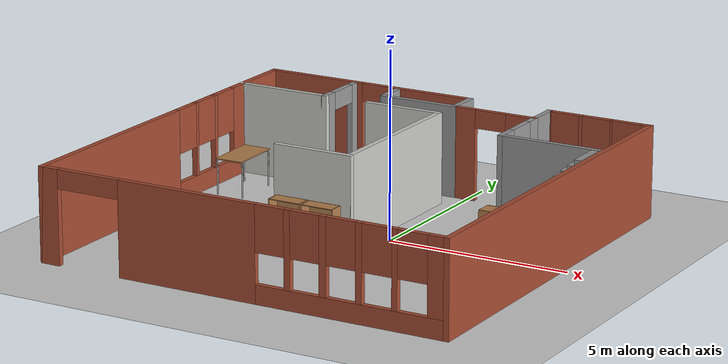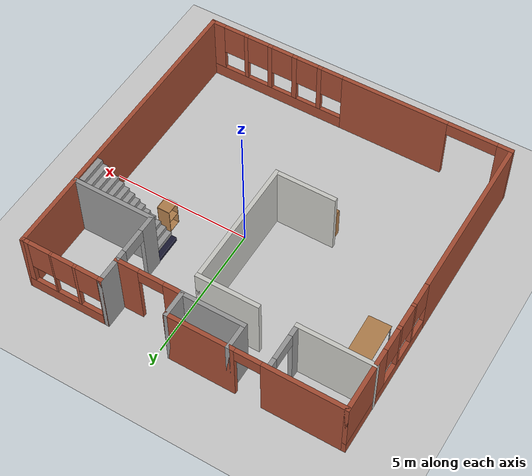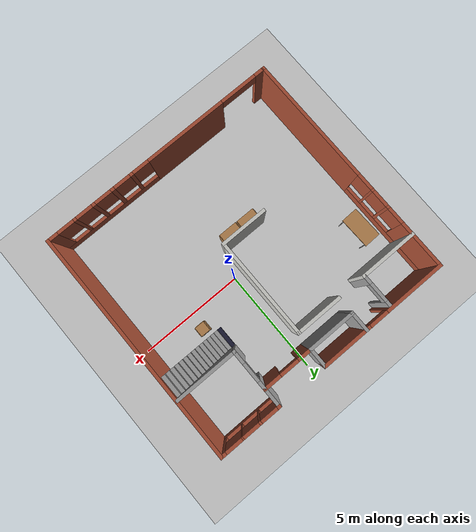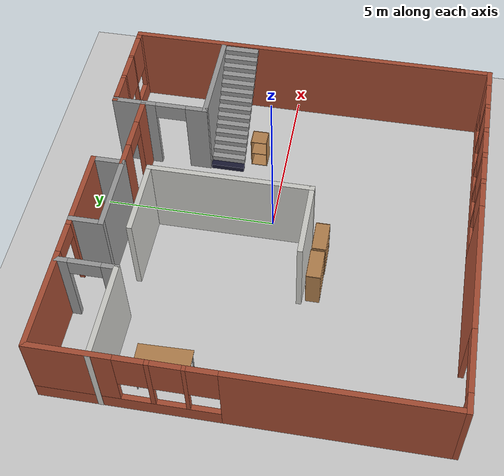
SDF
<sdf version="1.6">
 <world name="default">
  <light name="sun" type="directional">
   <pose>0 0 10 0 -0 0</pose>
   <diffuse>0.8 0.8 0.8 1</diffuse>
   <specular>0.2 0.2 0.2 1</specular>
   <attenuation>
    <range>1000</range>
    <constant>0.9</constant>
    <linear>0.01</linear>
    <quadratic>0.001</quadratic>
   </attenuation>
   <direction>-0.5 0.1 -0.9</direction>
  </light>
  <model name="ground_plane">
   <static>1</static>
   <link name="link">
    <collision name="collision">
     <geometry><plane><normal>0 0 1</normal><size>100 100</size></plane></geometry>
     <surface><friction><ode><mu>100</mu><mu2>50</mu2></ode></friction></surface>
    </collision>
    <visual name="visual">
     <cast_shadows>0</cast_shadows>
     <geometry><plane><normal>0 0 1</normal><size>100 100</size></plane></geometry>
     <material>
      <script><uri>file://media/materials/scripts/gazebo.material</uri><name>Gazebo/Grey</name></script>
     </material>
    </visual>
   </link>
  </model>
  <gravity>0 0 -9.8</gravity>
  <magnetic_field>6e-06 2.3e-05 -4.2e-05</magnetic_field>
  <atmosphere type="adiabatic"/>
  <physics name="default_physics" default="0" type="ode">
   <max_step_size>0.001</max_step_size>
   <real_time_factor>1</real_time_factor>
   <real_time_update_rate>1000</real_time_update_rate>
  </physics>
  <scene><ambient>0.4 0.4 0.4 1</ambient><background>0.7 0.7 0.7 1</background><shadows>1</shadows></scene>
  <spherical_coordinates>
   <surface_model>EARTH_WGS84</surface_model>
   <latitude_deg>0</latitude_deg>
   <longitude_deg>0</longitude_deg>
   <elevation>0</elevation>
   <heading_deg>0</heading_deg>
  </spherical_coordinates>
  <model name="bookshelf">
   <static>1</static>
   <link name="link">
    <inertial><mass>1</mass></inertial>
    <collision name="back">
     <pose>0 0.005 0.6 0 -0 0</pose>
     <geometry><box><size>0.9 0.01 1.2</size></box></geometry>
    </collision>
    <visual name="visual1">
     <pose>0 0.005 0.6 0 -0 0</pose>
     <geometry><box><size>0.9 0.01 1.2</size></box></geometry>
     <material>
      <script><uri>file://media/materials/scripts/gazebo.material</uri><name>Gazebo/Wood</name></script>
     </material>
    </visual>
    <collision name="left_side">
     <pose>0.45 -0.195 0.6 0 -0 0</pose>
     <geometry><box><size>0.02 0.4 1.2</size></box></geometry>
    </collision>
    <visual name="visual2">
     <pose>0.45 -0.195 0.6 0 -0 0</pose>
     <geometry><box><size>0.02 0.4 1.2</size></box></geometry>
     <material>
      <script><uri>file://media/materials/scripts/gazebo.material</uri><name>Gazebo/Wood</name></script>
     </material>
    </visual>
    <collision name="right_side">
     <pose>-0.45 -0.195 0.6 0 -0 0</pose>
     <geometry><box><size>0.02 0.4 1.2</size></box></geometry>
    </collision>
    <visual name="visual3">
     <pose>-0.45 -0.195 0.6 0 -0 0</pose>
     <geometry><box><size>0.02 0.4 1.2</size></box></geometry>
     <material>
      <script><uri>file://media/materials/scripts/gazebo.material</uri><name>Gazebo/Wood</name></script>
     </material>
    </visual>
    <collision name="bottom">
     <pose>0 -0.195 0.03 0 -0 0</pose>
     <geometry><box><size>0.88 0.4 0.06</size></box></geometry>
    </collision>
    <visual name="visual4">
     <pose>0 -0.195 0.03 0 -0 0</pose>
     <geometry><box><size>0.88 0.4 0.06</size></box></geometry>
     <material>
      <script><uri>file://media/materials/scripts/gazebo.material</uri><name>Gazebo/Wood</name></script>
     </material>
    </visual>
    <collision name="top">
     <pose>0 -0.195 1.19 0 -0 0</pose>
     <geometry><box><size>0.88 0.4 0.02</size></box></geometry>
    </collision>
    <visual name="visual5">
     <pose>0 -0.195 1.19 0 -0 0</pose>
     <geometry><box><size>0.88 0.4 0.02</size></box></geometry>
     <material>
      <script><uri>file://media/materials/scripts/gazebo.material</uri><name>Gazebo/Wood</name></script>
     </material>
    </visual>
    <collision name="low_shelf">
     <pose>0 -0.195 0.43 0 -0 0</pose>
     <geometry><box><size>0.88 0.4 0.02</size></box></geometry>
    </collision>
    <visual name="visual6">
     <pose>0 -0.195 0.43 0 -0 0</pose>
     <geometry><box><size>0.88 0.4 0.02</size></box></geometry>
     <material>
      <script><uri>file://media/materials/scripts/gazebo.material</uri><name>Gazebo/Wood</name></script>
     </material>
    </visual>
    <collision name="high_shelf">
     <pose>0 -0.195 0.8 0 -0 0</pose>
     <geometry><box><size>0.88 0.4 0.02</size></box></geometry>
    </collision>
    <visual name="visual7">
     <pose>0 -0.195 0.8 0 -0 0</pose>
     <geometry><box><size>0.88 0.4 0.02</size></box></geometry>
     <material>
      <script><uri>file://media/materials/scripts/gazebo.material</uri><name>Gazebo/Wood</name></script>
     </material>
    </visual>
   </link>
   <pose>-2.07117 -1.36987 0 0 -0 0</pose>
  </model>
  <model name="bookshelf_0">
   <static>1</static>
   <link name="link">
    <inertial><mass>1</mass></inertial>
    <collision name="back">
     <pose>0 0.005 0.6 0 -0 0</pose>
     <geometry><box><size>0.9 0.01 1.2</size></box></geometry>
    </collision>
    <visual name="visual1">
     <pose>0 0.005 0.6 0 -0 0</pose>
     <geometry><box><size>0.9 0.01 1.2</size></box></geometry>
     <material>
      <script><uri>file://media/materials/scripts/gazebo.material</uri><name>Gazebo/Wood</name></script>
     </material>
    </visual>
    <collision name="left_side">
     <pose>0.45 -0.195 0.6 0 -0 0</pose>
     <geometry><box><size>0.02 0.4 1.2</size></box></geometry>
    </collision>
    <visual name="visual2">
     <pose>0.45 -0.195 0.6 0 -0 0</pose>
     <geometry><box><size>0.02 0.4 1.2</size></box></geometry>
     <material>
      <script><uri>file://media/materials/scripts/gazebo.material</uri><name>Gazebo/Wood</name></script>
     </material>
    </visual>
    <collision name="right_side">
     <pose>-0.45 -0.195 0.6 0 -0 0</pose>
     <geometry><box><size>0.02 0.4 1.2</size></box></geometry>
    </collision>
    <visual name="visual3">
     <pose>-0.45 -0.195 0.6 0 -0 0</pose>
     <geometry><box><size>0.02 0.4 1.2</size></box></geometry>
     <material>
      <script><uri>file://media/materials/scripts/gazebo.material</uri><name>Gazebo/Wood</name></script>
     </material>
    </visual>
    <collision name="bottom">
     <pose>0 -0.195 0.03 0 -0 0</pose>
     <geometry><box><size>0.88 0.4 0.06</size></box></geometry>
    </collision>
    <visual name="visual4">
     <pose>0 -0.195 0.03 0 -0 0</pose>
     <geometry><box><size>0.88 0.4 0.06</size></box></geometry>
     <material>
      <script><uri>file://media/materials/scripts/gazebo.material</uri><name>Gazebo/Wood</name></script>
     </material>
    </visual>
    <collision name="top">
     <pose>0 -0.195 1.19 0 -0 0</pose>
     <geometry><box><size>0.88 0.4 0.02</size></box></geometry>
    </collision>
    <visual name="visual5">
     <pose>0 -0.195 1.19 0 -0 0</pose>
     <geometry><box><size>0.88 0.4 0.02</size></box></geometry>
     <material>
      <script><uri>file://media/materials/scripts/gazebo.material</uri><name>Gazebo/Wood</name></script>
     </material>
    </visual>
    <collision name="low_shelf">
     <pose>0 -0.195 0.43 0 -0 0</pose>
     <geometry><box><size>0.88 0.4 0.02</size></box></geometry>
    </collision>
    <visual name="visual6">
     <pose>0 -0.195 0.43 0 -0 0</pose>
     <geometry><box><size>0.88 0.4 0.02</size></box></geometry>
     <material>
      <script><uri>file://media/materials/scripts/gazebo.material</uri><name>Gazebo/Wood</name></script>
     </material>
    </visual>
    <collision name="high_shelf">
     <pose>0 -0.195 0.8 0 -0 0</pose>
     <geometry><box><size>0.88 0.4 0.02</size></box></geometry>
    </collision>
    <visual name="visual7">
     <pose>0 -0.195 0.8 0 -0 0</pose>
     <geometry><box><size>0.88 0.4 0.02</size></box></geometry>
     <material>
      <script><uri>file://media/materials/scripts/gazebo.material</uri><name>Gazebo/Wood</name></script>
     </material>
    </visual>
   </link>
   <pose>-1.10888 -1.38227 0 0 -0 0</pose>
  </model>
  <model name="cabinet">
   <static>1</static>
   <link name="cabinet_bottom_plate">
    <inertial>
     <pose>0 0 -1 0 -0 0</pose>
     <inertia><ixx>2.05</ixx><ixy>0</ixy><ixz>0</ixz><iyy>2.05</iyy><iyz>0</iyz><izz>2.05</izz></inertia>
     <mass>25</mass>
    </inertial>
    <collision name="cabinet_bottom_plate_geom">
     <pose>0 0 0.01 0 -0 0</pose>
     <geometry><box><size>0.45 0.45 0.02</size></box></geometry>
    </collision>
    <visual name="cabinet_bottom_plate_geom_visual">
     <pose>0 0 0.01 0 -0 0</pose>
     <geometry><box><size>0.45 0.45 0.02</size></box></geometry>
     <material>
      <script><uri>file://media/materials/scripts/gazebo.material</uri><name>Gazebo/Wood</name></script>
     </material>
    </visual>
    <collision name="cabinet_bottom_plate_geom_cabinet_back_plate">
     <pose>0.235 0 0.51 0 -0 0</pose>
     <geometry><box><size>0.02 0.45 1.02</size></box></geometry>
    </collision>
    <visual name="cabinet_bottom_plate_geom_cabinet_back_plate_visual">
     <pose>0.235 0 0.51 0 -0 0</pose>
     <geometry><box><size>0.02 0.45 1.02</size></box></geometry>
     <material>
      <script><uri>file://media/materials/scripts/gazebo.material</uri><name>Gazebo/Wood</name></script>
     </material>
    </visual>
    <collision name="cabinet_bottom_plate_geom_cabinet_left_plate">
     <pose>0 0.235 0.51 0 -0 0</pose>
     <geometry><box><size>0.45 0.02 1.02</size></box></geometry>
    </collision>
    <visual name="cabinet_bottom_plate_geom_cabinet_left_plate_visual">
     <pose>0 0.235 0.51 0 -0 0</pose>
     <geometry><box><size>0.45 0.02 1.02</size></box></geometry>
     <material>
      <script><uri>file://media/materials/scripts/gazebo.material</uri><name>Gazebo/Wood</name></script>
     </material>
    </visual>
    <collision name="cabinet_bottom_plate_geom_cabinet_middle_plate">
     <pose>0 0 0.51 0 -0 0</pose>
     <geometry><box><size>0.45 0.45 0.02</size></box></geometry>
    </collision>
    <visual name="cabinet_bottom_plate_geom_cabinet_middle_plate_visual">
     <pose>0 0 0.51 0 -0 0</pose>
     <geometry><box><size>0.45 0.45 0.02</size></box></geometry>
     <material>
      <script><uri>file://media/materials/scripts/gazebo.material</uri><name>Gazebo/Wood</name></script>
     </material>
    </visual>
    <collision name="cabinet_bottom_plate_geom_cabinet_right_plate">
     <pose>0 -0.235 0.51 0 -0 0</pose>
     <geometry><box><size>0.45 0.02 1.02</size></box></geometry>
    </collision>
    <visual name="cabinet_bottom_plate_geom_cabinet_right_plate_visual">
     <pose>0 -0.235 0.51 0 -0 0</pose>
     <geometry><box><size>0.45 0.02 1.02</size></box></geometry>
     <material>
      <script><uri>file://media/materials/scripts/gazebo.material</uri><name>Gazebo/Wood</name></script>
     </material>
    </visual>
    <collision name="cabinet_bottom_plate_geom_cabinet_top_plate">
     <pose>0 0 1.01 0 -0 0</pose>
     <geometry><box><size>0.45 0.45 0.02</size></box></geometry>
    </collision>
    <visual name="cabinet_bottom_plate_geom_cabinet_top_plate_visual">
     <pose>0 0 1.01 0 -0 0</pose>
     <geometry><box><size>0.45 0.45 0.02</size></box></geometry>
     <material>
      <script><uri>file://media/materials/scripts/gazebo.material</uri><name>Gazebo/Wood</name></script>
     </material>
    </visual>
   </link>
   <pose>2.44272 0.813609 0 0 -0 0</pose>
  </model>
  <model name="table">
   <static>1</static>
   <link name="link">
    <collision name="surface">
     <pose>0 0 1 0 -0 0</pose>
     <geometry><box><size>1.5 0.8 0.03</size></box></geometry>
     <surface><friction><ode><mu>0.6</mu><mu2>0.6</mu2></ode></friction></surface>
    </collision>
    <visual name="visual1">
     <pose>0 0 1 0 -0 0</pose>
     <geometry><box><size>1.5 0.8 0.03</size></box></geometry>
     <material>
      <script><uri>file://media/materials/scripts/gazebo.material</uri><name>Gazebo/Wood</name></script>
     </material>
    </visual>
    <collision name="front_left_leg">
     <pose>0.68 0.38 0.5 0 -0 0</pose>
     <geometry><cylinder><radius>0.02</radius><length>1</length></cylinder></geometry>
    </collision>
    <visual name="front_left_leg">
     <pose>0.68 0.38 0.5 0 -0 0</pose>
     <geometry><cylinder><radius>0.02</radius><length>1</length></cylinder></geometry>
     <material>
      <script><uri>file://media/materials/scripts/gazebo.material</uri><name>Gazebo/Grey</name></script>
     </material>
    </visual>
    <collision name="front_right_leg">
     <pose>0.68 -0.38 0.5 0 -0 0</pose>
     <geometry><cylinder><radius>0.02</radius><length>1</length></cylinder></geometry>
    </collision>
    <visual name="front_right_leg">
     <pose>0.68 -0.38 0.5 0 -0 0</pose>
     <geometry><cylinder><radius>0.02</radius><length>1</length></cylinder></geometry>
     <material>
      <script><uri>file://media/materials/scripts/gazebo.material</uri><name>Gazebo/Grey</name></script>
     </material>
    </visual>
    <collision name="back_right_leg">
     <pose>-0.68 -0.38 0.5 0 -0 0</pose>
     <geometry><cylinder><radius>0.02</radius><length>1</length></cylinder></geometry>
    </collision>
    <visual name="back_right_leg">
     <pose>-0.68 -0.38 0.5 0 -0 0</pose>
     <geometry><cylinder><radius>0.02</radius><length>1</length></cylinder></geometry>
     <material>
      <script><uri>file://media/materials/scripts/gazebo.material</uri><name>Gazebo/Grey</name></script>
     </material>
    </visual>
    <collision name="back_left_leg">
     <pose>-0.68 0.38 0.5 0 -0 0</pose>
     <geometry><cylinder><radius>0.02</radius><length>1</length></cylinder></geometry>
    </collision>
    <visual name="back_left_leg">
     <pose>-0.68 0.38 0.5 0 -0 0</pose>
     <geometry><cylinder><radius>0.02</radius><length>1</length></cylinder></geometry>
     <material>
      <script><uri>file://media/materials/scripts/gazebo.material</uri><name>Gazebo/Grey</name></script>
     </material>
    </visual>
   </link>
   <pose>-5.60379 1.89349 0 0 0 -1.54503</pose>
  </model>
  <model name="project1_building">
   <link name="Stairs_7">
    <inertial>
     <mass>1</mass>
     <inertia><ixx>1</ixx><ixy>0</ixy><ixz>0</ixz><iyy>1</iyy><iyz>0</iyz><izz>1</izz></inertia>
    </inertial>
    <visual name="Stairs_7_Visual_0">
     <material>
      <ambient>0.1 0.1 0.1 1</ambient>
      <diffuse>0.1 0.1 0.2 1</diffuse>
      <specular>0 0 0 1</specular>
      <emissive>0 0 0 1</emissive>
      <shader type="pixel"><normal_map>__default__</normal_map></shader>
      <script><name>ModelPreview_1::Stairs_7::Stairs_7_Visual_0_MATERIAL_</name><uri>__default__</uri></script>
     </material>
     <pose>2.81269 2.1369 0.083333 0 -0 1.5708</pose>
     <geometry><box><size>1 0.19 0.166667</size></box></geometry>
     <material>
      <script><uri>file://media/materials/scripts/gazebo.material</uri><name>Gazebo/Grey</name></script>
      <ambient>1 1 1 1</ambient>
     </material>
     <meta><layer>0</layer></meta>
    </visual>
    <visual name="Stairs_7_Visual_1">
     <pose>3.00269 2.1369 0.25 0 -0 1.5708</pose>
     <geometry><box><size>1 0.19 0.166667</size></box></geometry>
     <material>
      <script><uri>file://media/materials/scripts/gazebo.material</uri><name>Gazebo/Grey</name></script>
      <ambient>1 1 1 1</ambient>
      <shader type="pixel"><normal_map>__default__</normal_map></shader>
      <diffuse>0.7 0.7 0.7 1</diffuse>
      <specular>0.01 0.01 0.01 1</specular>
      <emissive>0 0 0 1</emissive>
     </material>
     <meta><layer>0</layer></meta>
    </visual>
    <visual name="Stairs_7_Visual_2">
     <pose>3.19269 2.1369 0.416667 0 -0 1.5708</pose>
     <geometry><box><size>1 0.19 0.166667</size></box></geometry>
     <material>
      <script><uri>file://media/materials/scripts/gazebo.material</uri><name>Gazebo/Grey</name></script>
      <ambient>1 1 1 1</ambient>
      <shader type="pixel"><normal_map>__default__</normal_map></shader>
      <diffuse>0.7 0.7 0.7 1</diffuse>
      <specular>0.01 0.01 0.01 1</specular>
      <emissive>0 0 0 1</emissive>
     </material>
     <meta><layer>0</layer></meta>
    </visual>
    <visual name="Stairs_7_Visual_3">
     <pose>3.38269 2.1369 0.583333 0 -0 1.5708</pose>
     <geometry><box><size>1 0.19 0.166667</size></box></geometry>
     <material>
      <script><uri>file://media/materials/scripts/gazebo.material</uri><name>Gazebo/Grey</name></script>
      <ambient>1 1 1 1</ambient>
      <shader type="pixel"><normal_map>__default__</normal_map></shader>
      <diffuse>0.7 0.7 0.7 1</diffuse>
      <specular>0.01 0.01 0.01 1</specular>
      <emissive>0 0 0 1</emissive>
     </material>
     <meta><layer>0</layer></meta>
    </visual>
    <visual name="Stairs_7_Visual_4">
     <pose>3.57269 2.1369 0.75 0 -0 1.5708</pose>
     <geometry><box><size>1 0.19 0.166667</size></box></geometry>
     <material>
      <script><uri>file://media/materials/scripts/gazebo.material</uri><name>Gazebo/Grey</name></script>
      <ambient>1 1 1 1</ambient>
      <shader type="pixel"><normal_map>__default__</normal_map></shader>
      <diffuse>0.7 0.7 0.7 1</diffuse>
      <specular>0.01 0.01 0.01 1</specular>
      <emissive>0 0 0 1</emissive>
     </material>
     <meta><layer>0</layer></meta>
    </visual>
    <visual name="Stairs_7_Visual_5">
     <pose>3.76269 2.1369 0.916667 0 -0 1.5708</pose>
     <geometry><box><size>1 0.19 0.166667</size></box></geometry>
     <material>
      <script><uri>file://media/materials/scripts/gazebo.material</uri><name>Gazebo/Grey</name></script>
      <ambient>1 1 1 1</ambient>
      <shader type="pixel"><normal_map>__default__</normal_map></shader>
      <diffuse>0.7 0.7 0.7 1</diffuse>
      <specular>0.01 0.01 0.01 1</specular>
      <emissive>0 0 0 1</emissive>
     </material>
     <meta><layer>0</layer></meta>
    </visual>
    <visual name="Stairs_7_Visual_6">
     <pose>3.95269 2.1369 1.08333 0 -0 1.5708</pose>
     <geometry><box><size>1 0.19 0.166667</size></box></geometry>
     <material>
      <script><uri>file://media/materials/scripts/gazebo.material</uri><name>Gazebo/Grey</name></script>
      <ambient>1 1 1 1</ambient>
      <shader type="pixel"><normal_map>__default__</normal_map></shader>
      <diffuse>0.7 0.7 0.7 1</diffuse>
      <specular>0.01 0.01 0.01 1</specular>
      <emissive>0 0 0 1</emissive>
     </material>
     <meta><layer>0</layer></meta>
    </visual>
    <visual name="Stairs_7_Visual_7">
     <pose>4.14269 2.1369 1.25 0 -0 1.5708</pose>
     <geometry><box><size>1 0.19 0.166667</size></box></geometry>
     <material>
      <script><uri>file://media/materials/scripts/gazebo.material</uri><name>Gazebo/Grey</name></script>
      <ambient>1 1 1 1</ambient>
      <shader type="pixel"><normal_map>__default__</normal_map></shader>
      <diffuse>0.7 0.7 0.7 1</diffuse>
      <specular>0.01 0.01 0.01 1</specular>
      <emissive>0 0 0 1</emissive>
     </material>
     <meta><layer>0</layer></meta>
    </visual>
    <visual name="Stairs_7_Visual_8">
     <pose>4.33269 2.1369 1.41667 0 -0 1.5708</pose>
     <geometry><box><size>1 0.19 0.166667</size></box></geometry>
     <material>
      <script><uri>file://media/materials/scripts/gazebo.material</uri><name>Gazebo/Grey</name></script>
      <ambient>1 1 1 1</ambient>
      <shader type="pixel"><normal_map>__default__</normal_map></shader>
      <diffuse>0.7 0.7 0.7 1</diffuse>
      <specular>0.01 0.01 0.01 1</specular>
      <emissive>0 0 0 1</emissive>
     </material>
     <meta><layer>0</layer></meta>
    </visual>
    <visual name="Stairs_7_Visual_9">
     <pose>4.52269 2.1369 1.58333 0 -0 1.5708</pose>
     <geometry><box><size>1 0.19 0.166667</size></box></geometry>
     <material>
      <script><uri>file://media/materials/scripts/gazebo.material</uri><name>Gazebo/Grey</name></script>
      <ambient>1 1 1 1</ambient>
      <shader type="pixel"><normal_map>__default__</normal_map></shader>
      <diffuse>0.7 0.7 0.7 1</diffuse>
      <specular>0.01 0.01 0.01 1</specular>
      <emissive>0 0 0 1</emissive>
     </material>
     <meta><layer>0</layer></meta>
    </visual>
    <visual name="Stairs_7_Visual_10">
     <pose>4.71269 2.1369 1.75 0 -0 1.5708</pose>
     <geometry><box><size>1 0.19 0.166667</size></box></geometry>
     <material>
      <script><uri>file://media/materials/scripts/gazebo.material</uri><name>Gazebo/Grey</name></script>
      <ambient>1 1 1 1</ambient>
      <shader type="pixel"><normal_map>__default__</normal_map></shader>
      <diffuse>0.7 0.7 0.7 1</diffuse>
      <specular>0.01 0.01 0.01 1</specular>
      <emissive>0 0 0 1</emissive>
     </material>
     <meta><layer>0</layer></meta>
    </visual>
    <visual name="Stairs_7_Visual_11">
     <pose>4.90269 2.1369 1.91667 0 -0 1.5708</pose>
     <geometry><box><size>1 0.19 0.166667</size></box></geometry>
     <material>
      <script><uri>file://media/materials/scripts/gazebo.material</uri><name>Gazebo/Grey</name></script>
      <ambient>1 1 1 1</ambient>
      <shader type="pixel"><normal_map>__default__</normal_map></shader>
      <diffuse>0.7 0.7 0.7 1</diffuse>
      <specular>0.01 0.01 0.01 1</specular>
      <emissive>0 0 0 1</emissive>
     </material>
     <meta><layer>0</layer></meta>
    </visual>
    <visual name="Stairs_7_Visual_12">
     <pose>5.09269 2.1369 2.08333 0 -0 1.5708</pose>
     <geometry><box><size>1 0.19 0.166667</size></box></geometry>
     <material>
      <script><uri>file://media/materials/scripts/gazebo.material</uri><name>Gazebo/Grey</name></script>
      <ambient>1 1 1 1</ambient>
      <shader type="pixel"><normal_map>__default__</normal_map></shader>
      <diffuse>0.7 0.7 0.7 1</diffuse>
      <specular>0.01 0.01 0.01 1</specular>
      <emissive>0 0 0 1</emissive>
     </material>
     <meta><layer>0</layer></meta>
    </visual>
    <visual name="Stairs_7_Visual_13">
     <pose>5.28269 2.1369 2.25 0 -0 1.5708</pose>
     <geometry><box><size>1 0.19 0.166667</size></box></geometry>
     <material>
      <script><uri>file://media/materials/scripts/gazebo.material</uri><name>Gazebo/Grey</name></script>
      <ambient>1 1 1 1</ambient>
      <shader type="pixel"><normal_map>__default__</normal_map></shader>
      <diffuse>0.7 0.7 0.7 1</diffuse>
      <specular>0.01 0.01 0.01 1</specular>
      <emissive>0 0 0 1</emissive>
     </material>
     <meta><layer>0</layer></meta>
    </visual>
    <visual name="Stairs_7_Visual_14">
     <pose>5.47269 2.1369 2.41667 0 -0 1.5708</pose>
     <geometry><box><size>1 0.19 0.166667</size></box></geometry>
     <material>
      <script><uri>file://media/materials/scripts/gazebo.material</uri><name>Gazebo/Grey</name></script>
      <ambient>1 1 1 1</ambient>
      <shader type="pixel"><normal_map>__default__</normal_map></shader>
      <diffuse>0.7 0.7 0.7 1</diffuse>
      <specular>0.01 0.01 0.01 1</specular>
      <emissive>0 0 0 1</emissive>
     </material>
     <meta><layer>0</layer></meta>
    </visual>
    <collision name="Stairs_7_Collision_0">
     <pose>2.81269 2.1369 0.083333 0 -0 1.5708</pose>
     <geometry><box><size>1 0.19 0.166667</size></box></geometry>
     <surface>
      <friction>
       <ode><mu>1</mu><mu2>1</mu2><fdir1>0 0 0</fdir1><slip1>0</slip1><slip2>0</slip2></ode>
       <torsional>
        <coefficient>1</coefficient>
        <patch_radius>0</patch_radius>
        <surface_radius>0</surface_radius>
        <use_patch_radius>1</use_patch_radius>
        <ode><slip>0</slip></ode>
       </torsional>
      </friction>
      <bounce><restitution_coefficient>0</restitution_coefficient><threshold>1e+06</threshold></bounce>
      <contact>
       <collide_without_contact>0</collide_without_contact>
       <collide_without_contact_bitmask>1</collide_without_contact_bitmask>
       <collide_bitmask>1</collide_bitmask>
       <ode>
        <soft_cfm>0</soft_cfm>
        <soft_erp>0.2</soft_erp>
        <kp>1e+13</kp>
        <kd>1</kd>
        <max_vel>0.01</max_vel>
        <min_depth>0</min_depth>
       </ode>
       <bullet>
        <split_impulse>1</split_impulse>
        <split_impulse_penetration_threshold>-0.01</split_impulse_penetration_threshold>
        <soft_cfm>0</soft_cfm>
        <soft_erp>0.2</soft_erp>
        <kp>1e+13</kp>
        <kd>1</kd>
       </bullet>
      </contact>
     </surface>
    </collision>
    <collision name="Stairs_7_Collision_1">
     <pose>3.00269 2.1369 0.25 0 -0 1.5708</pose>
     <geometry><box><size>1 0.19 0.166667</size></box></geometry>
     <surface>
      <friction>
       <ode><mu>1</mu><mu2>1</mu2><fdir1>0 0 0</fdir1><slip1>0</slip1><slip2>0</slip2></ode>
       <torsional>
        <coefficient>1</coefficient>
        <patch_radius>0</patch_radius>
        <surface_radius>0</surface_radius>
        <use_patch_radius>1</use_patch_radius>
        <ode><slip>0</slip></ode>
       </torsional>
      </friction>
      <bounce><restitution_coefficient>0</restitution_coefficient><threshold>1e+06</threshold></bounce>
      <contact>
       <collide_without_contact>0</collide_without_contact>
       <collide_without_contact_bitmask>1</collide_without_contact_bitmask>
       <collide_bitmask>1</collide_bitmask>
       <ode>
        <soft_cfm>0</soft_cfm>
        <soft_erp>0.2</soft_erp>
        <kp>1e+13</kp>
        <kd>1</kd>
        <max_vel>0.01</max_vel>
        <min_depth>0</min_depth>
       </ode>
       <bullet>
        <split_impulse>1</split_impulse>
        <split_impulse_penetration_threshold>-0.01</split_impulse_penetration_threshold>
        <soft_cfm>0</soft_cfm>
        <soft_erp>0.2</soft_erp>
        <kp>1e+13</kp>
        <kd>1</kd>
       </bullet>
      </contact>
     </surface>
    </collision>
    <collision name="Stairs_7_Collision_2">
     <pose>3.19269 2.1369 0.416667 0 -0 1.5708</pose>
     <geometry><box><size>1 0.19 0.166667</size></box></geometry>
     <surface>
      <friction>
       <ode><mu>1</mu><mu2>1</mu2><fdir1>0 0 0</fdir1><slip1>0</slip1><slip2>0</slip2></ode>
       <torsional>
        <coefficient>1</coefficient>
        <patch_radius>0</patch_radius>
        <surface_radius>0</surface_radius>
        <use_patch_radius>1</use_patch_radius>
        <ode><slip>0</slip></ode>
       </torsional>
      </friction>
      <bounce><restitution_coefficient>0</restitution_coefficient><threshold>1e+06</threshold></bounce>
      <contact>
       <collide_without_contact>0</collide_without_contact>
       <collide_without_contact_bitmask>1</collide_without_contact_bitmask>
       <collide_bitmask>1</collide_bitmask>
       <ode>
        <soft_cfm>0</soft_cfm>
        <soft_erp>0.2</soft_erp>
        <kp>1e+13</kp>
        <kd>1</kd>
        <max_vel>0.01</max_vel>
        <min_depth>0</min_depth>
       </ode>
       <bullet>
        <split_impulse>1</split_impulse>
        <split_impulse_penetration_threshold>-0.01</split_impulse_penetration_threshold>
        <soft_cfm>0</soft_cfm>
        <soft_erp>0.2</soft_erp>
        <kp>1e+13</kp>
        <kd>1</kd>
       </bullet>
      </contact>
     </surface>
    </collision>
    <collision name="Stairs_7_Collision_3">
     <pose>3.38269 2.1369 0.583333 0 -0 1.5708</pose>
     <geometry><box><size>1 0.19 0.166667</size></box></geometry>
     <surface>
      <friction>
       <ode><mu>1</mu><mu2>1</mu2><fdir1>0 0 0</fdir1><slip1>0</slip1><slip2>0</slip2></ode>
       <torsional>
        <coefficient>1</coefficient>
        <patch_radius>0</patch_radius>
        <surface_radius>0</surface_radius>
        <use_patch_radius>1</use_patch_radius>
        <ode><slip>0</slip></ode>
       </torsional>
      </friction>
      <bounce><restitution_coefficient>0</restitution_coefficient><threshold>1e+06</threshold></bounce>
      <contact>
       <collide_without_contact>0</collide_without_contact>
       <collide_without_contact_bitmask>1</collide_without_contact_bitmask>
       <collide_bitmask>1</collide_bitmask>
       <ode>
        <soft_cfm>0</soft_cfm>
        <soft_erp>0.2</soft_erp>
        <kp>1e+13</kp>
        <kd>1</kd>
        <max_vel>0.01</max_vel>
        <min_depth>0</min_depth>
       </ode>
       <bullet>
        <split_impulse>1</split_impulse>
        <split_impulse_penetration_threshold>-0.01</split_impulse_penetration_threshold>
        <soft_cfm>0</soft_cfm>
        <soft_erp>0.2</soft_erp>
        <kp>1e+13</kp>
        <kd>1</kd>
       </bullet>
      </contact>
     </surface>
    </collision>
    <collision name="Stairs_7_Collision_4">
     <pose>3.57269 2.1369 0.75 0 -0 1.5708</pose>
     <geometry><box><size>1 0.19 0.166667</size></box></geometry>
     <surface>
      <friction>
       <ode><mu>1</mu><mu2>1</mu2><fdir1>0 0 0</fdir1><slip1>0</slip1><slip2>0</slip2></ode>
       <torsional>
        <coefficient>1</coefficient>
        <patch_radius>0</patch_radius>
        <surface_radius>0</surface_radius>
        <use_patch_radius>1</use_patch_radius>
        <ode><slip>0</slip></ode>
       </torsional>
      </friction>
      <bounce><restitution_coefficient>0</restitution_coefficient><threshold>1e+06</threshold></bounce>
      <contact>
       <collide_without_contact>0</collide_without_contact>
       <collide_without_contact_bitmask>1</collide_without_contact_bitmask>
       <collide_bitmask>1</collide_bitmask>
       <ode>
        <soft_cfm>0</soft_cfm>
        <soft_erp>0.2</soft_erp>
        <kp>1e+13</kp>
        <kd>1</kd>
        <max_vel>0.01</max_vel>
        <min_depth>0</min_depth>
       </ode>
       <bullet>
        <split_impulse>1</split_impulse>
        <split_impulse_penetration_threshold>-0.01</split_impulse_penetration_threshold>
        <soft_cfm>0</soft_cfm>
        <soft_erp>0.2</soft_erp>
        <kp>1e+13</kp>
        <kd>1</kd>
       </bullet>
      </contact>
     </surface>
    </collision>
    <collision name="Stairs_7_Collision_5">
     <pose>3.76269 2.1369 0.916667 0 -0 1.5708</pose>
     <geometry><box><size>1 0.19 0.166667</size></box></geometry>
     <surface>
      <friction>
       <ode><mu>1</mu><mu2>1</mu2><fdir1>0 0 0</fdir1><slip1>0</slip1><slip2>0</slip2></ode>
       <torsional>
        <coefficient>1</coefficient>
        <patch_radius>0</patch_radius>
        <surface_radius>0</surface_radius>
        <use_patch_radius>1</use_patch_radius>
        <ode><slip>0</slip></ode>
       </torsional>
      </friction>
      <bounce><restitution_coefficient>0</restitution_coefficient><threshold>1e+06</threshold></bounce>
      <contact>
       <collide_without_contact>0</collide_without_contact>
       <collide_without_contact_bitmask>1</collide_without_contact_bitmask>
       <collide_bitmask>1</collide_bitmask>
       <ode>
        <soft_cfm>0</soft_cfm>
        <soft_erp>0.2</soft_erp>
        <kp>1e+13</kp>
        <kd>1</kd>
        <max_vel>0.01</max_vel>
        <min_depth>0</min_depth>
       </ode>
       <bullet>
        <split_impulse>1</split_impulse>
        <split_impulse_penetration_threshold>-0.01</split_impulse_penetration_threshold>
        <soft_cfm>0</soft_cfm>
        <soft_erp>0.2</soft_erp>
        <kp>1e+13</kp>
        <kd>1</kd>
       </bullet>
      </contact>
     </surface>
    </collision>
    <collision name="Stairs_7_Collision_6">
     <pose>3.95269 2.1369 1.08333 0 -0 1.5708</pose>
     <geometry><box><size>1 0.19 0.166667</size></box></geometry>
     <surface>
      <friction>
       <ode><mu>1</mu><mu2>1</mu2><fdir1>0 0 0</fdir1><slip1>0</slip1><slip2>0</slip2></ode>
       <torsional>
        <coefficient>1</coefficient>
        <patch_radius>0</patch_radius>
        <surface_radius>0</surface_radius>
        <use_patch_radius>1</use_patch_radius>
        <ode><slip>0</slip></ode>
       </torsional>
      </friction>
      <bounce><restitution_coefficient>0</restitution_coefficient><threshold>1e+06</threshold></bounce>
      <contact>
       <collide_without_contact>0</collide_without_contact>
       <collide_without_contact_bitmask>1</collide_without_contact_bitmask>
       <collide_bitmask>1</collide_bitmask>
       <ode>
        <soft_cfm>0</soft_cfm>
        <soft_erp>0.2</soft_erp>
        <kp>1e+13</kp>
        <kd>1</kd>
        <max_vel>0.01</max_vel>
        <min_depth>0</min_depth>
       </ode>
       <bullet>
        <split_impulse>1</split_impulse>
        <split_impulse_penetration_threshold>-0.01</split_impulse_penetration_threshold>
        <soft_cfm>0</soft_cfm>
        <soft_erp>0.2</soft_erp>
        <kp>1e+13</kp>
        <kd>1</kd>
       </bullet>
      </contact>
     </surface>
    </collision>
    <collision name="Stairs_7_Collision_7">
     <pose>4.14269 2.1369 1.25 0 -0 1.5708</pose>
     <geometry><box><size>1 0.19 0.166667</size></box></geometry>
     <surface>
      <friction>
       <ode><mu>1</mu><mu2>1</mu2><fdir1>0 0 0</fdir1><slip1>0</slip1><slip2>0</slip2></ode>
       <torsional>
        <coefficient>1</coefficient>
        <patch_radius>0</patch_radius>
        <surface_radius>0</surface_radius>
        <use_patch_radius>1</use_patch_radius>
        <ode><slip>0</slip></ode>
       </torsional>
      </friction>
      <bounce><restitution_coefficient>0</restitution_coefficient><threshold>1e+06</threshold></bounce>
      <contact>
       <collide_without_contact>0</collide_without_contact>
       <collide_without_contact_bitmask>1</collide_without_contact_bitmask>
       <collide_bitmask>1</collide_bitmask>
       <ode>
        <soft_cfm>0</soft_cfm>
        <soft_erp>0.2</soft_erp>
        <kp>1e+13</kp>
        <kd>1</kd>
        <max_vel>0.01</max_vel>
        <min_depth>0</min_depth>
       </ode>
       <bullet>
        <split_impulse>1</split_impulse>
        <split_impulse_penetration_threshold>-0.01</split_impulse_penetration_threshold>
        <soft_cfm>0</soft_cfm>
        <soft_erp>0.2</soft_erp>
        <kp>1e+13</kp>
        <kd>1</kd>
       </bullet>
      </contact>
     </surface>
    </collision>
    <collision name="Stairs_7_Collision_8">
     <pose>4.33269 2.1369 1.41667 0 -0 1.5708</pose>
     <geometry><box><size>1 0.19 0.166667</size></box></geometry>
     <surface>
      <friction>
       <ode><mu>1</mu><mu2>1</mu2><fdir1>0 0 0</fdir1><slip1>0</slip1><slip2>0</slip2></ode>
       <torsional>
        <coefficient>1</coefficient>
        <patch_radius>0</patch_radius>
        <surface_radius>0</surface_radius>
        <use_patch_radius>1</use_patch_radius>
        <ode><slip>0</slip></ode>
       </torsional>
      </friction>
      <bounce><restitution_coefficient>0</restitution_coefficient><threshold>1e+06</threshold></bounce>
      <contact>
       <collide_without_contact>0</collide_without_contact>
       <collide_without_contact_bitmask>1</collide_without_contact_bitmask>
       <collide_bitmask>1</collide_bitmask>
       <ode>
        <soft_cfm>0</soft_cfm>
        <soft_erp>0.2</soft_erp>
        <kp>1e+13</kp>
        <kd>1</kd>
        <max_vel>0.01</max_vel>
        <min_depth>0</min_depth>
       </ode>
       <bullet>
        <split_impulse>1</split_impulse>
        <split_impulse_penetration_threshold>-0.01</split_impulse_penetration_threshold>
        <soft_cfm>0</soft_cfm>
        <soft_erp>0.2</soft_erp>
        <kp>1e+13</kp>
        <kd>1</kd>
       </bullet>
      </contact>
     </surface>
    </collision>
    <collision name="Stairs_7_Collision_9">
     <pose>4.52269 2.1369 1.58333 0 -0 1.5708</pose>
     <geometry><box><size>1 0.19 0.166667</size></box></geometry>
     <surface>
      <friction>
       <ode><mu>1</mu><mu2>1</mu2><fdir1>0 0 0</fdir1><slip1>0</slip1><slip2>0</slip2></ode>
       <torsional>
        <coefficient>1</coefficient>
        <patch_radius>0</patch_radius>
        <surface_radius>0</surface_radius>
        <use_patch_radius>1</use_patch_radius>
        <ode><slip>0</slip></ode>
       </torsional>
      </friction>
      <bounce><restitution_coefficient>0</restitution_coefficient><threshold>1e+06</threshold></bounce>
      <contact>
       <collide_without_contact>0</collide_without_contact>
       <collide_without_contact_bitmask>1</collide_without_contact_bitmask>
       <collide_bitmask>1</collide_bitmask>
       <ode>
        <soft_cfm>0</soft_cfm>
        <soft_erp>0.2</soft_erp>
        <kp>1e+13</kp>
        <kd>1</kd>
        <max_vel>0.01</max_vel>
        <min_depth>0</min_depth>
       </ode>
       <bullet>
        <split_impulse>1</split_impulse>
        <split_impulse_penetration_threshold>-0.01</split_impulse_penetration_threshold>
        <soft_cfm>0</soft_cfm>
        <soft_erp>0.2</soft_erp>
        <kp>1e+13</kp>
        <kd>1</kd>
       </bullet>
      </contact>
     </surface>
    </collision>
    <collision name="Stairs_7_Collision_10">
     <pose>4.71269 2.1369 1.75 0 -0 1.5708</pose>
     <geometry><box><size>1 0.19 0.166667</size></box></geometry>
     <surface>
      <friction>
       <ode><mu>1</mu><mu2>1</mu2><fdir1>0 0 0</fdir1><slip1>0</slip1><slip2>0</slip2></ode>
       <torsional>
        <coefficient>1</coefficient>
        <patch_radius>0</patch_radius>
        <surface_radius>0</surface_radius>
        <use_patch_radius>1</use_patch_radius>
        <ode><slip>0</slip></ode>
       </torsional>
      </friction>
      <bounce><restitution_coefficient>0</restitution_coefficient><threshold>1e+06</threshold></bounce>
      <contact>
       <collide_without_contact>0</collide_without_contact>
       <collide_without_contact_bitmask>1</collide_without_contact_bitmask>
       <collide_bitmask>1</collide_bitmask>
       <ode>
        <soft_cfm>0</soft_cfm>
        <soft_erp>0.2</soft_erp>
        <kp>1e+13</kp>
        <kd>1</kd>
        <max_vel>0.01</max_vel>
        <min_depth>0</min_depth>
       </ode>
       <bullet>
        <split_impulse>1</split_impulse>
        <split_impulse_penetration_threshold>-0.01</split_impulse_penetration_threshold>
        <soft_cfm>0</soft_cfm>
        <soft_erp>0.2</soft_erp>
        <kp>1e+13</kp>
        <kd>1</kd>
       </bullet>
      </contact>
     </surface>
    </collision>
    <collision name="Stairs_7_Collision_11">
     <pose>4.90269 2.1369 1.91667 0 -0 1.5708</pose>
     <geometry><box><size>1 0.19 0.166667</size></box></geometry>
     <surface>
      <friction>
       <ode><mu>1</mu><mu2>1</mu2><fdir1>0 0 0</fdir1><slip1>0</slip1><slip2>0</slip2></ode>
       <torsional>
        <coefficient>1</coefficient>
        <patch_radius>0</patch_radius>
        <surface_radius>0</surface_radius>
        <use_patch_radius>1</use_patch_radius>
        <ode><slip>0</slip></ode>
       </torsional>
      </friction>
      <bounce><restitution_coefficient>0</restitution_coefficient><threshold>1e+06</threshold></bounce>
      <contact>
       <collide_without_contact>0</collide_without_contact>
       <collide_without_contact_bitmask>1</collide_without_contact_bitmask>
       <collide_bitmask>1</collide_bitmask>
       <ode>
        <soft_cfm>0</soft_cfm>
        <soft_erp>0.2</soft_erp>
        <kp>1e+13</kp>
        <kd>1</kd>
        <max_vel>0.01</max_vel>
        <min_depth>0</min_depth>
       </ode>
       <bullet>
        <split_impulse>1</split_impulse>
        <split_impulse_penetration_threshold>-0.01</split_impulse_penetration_threshold>
        <soft_cfm>0</soft_cfm>
        <soft_erp>0.2</soft_erp>
        <kp>1e+13</kp>
        <kd>1</kd>
       </bullet>
      </contact>
     </surface>
    </collision>
    <collision name="Stairs_7_Collision_13">
     <pose>5.28269 2.1369 2.25 0 -0 1.5708</pose>
     <geometry><box><size>1 0.19 0.166667</size></box></geometry>
     <surface>
      <friction>
       <ode><mu>1</mu><mu2>1</mu2><fdir1>0 0 0</fdir1><slip1>0</slip1><slip2>0</slip2></ode>
       <torsional>
        <coefficient>1</coefficient>
        <patch_radius>0</patch_radius>
        <surface_radius>0</surface_radius>
        <use_patch_radius>1</use_patch_radius>
        <ode><slip>0</slip></ode>
       </torsional>
      </friction>
      <bounce><restitution_coefficient>0</restitution_coefficient><threshold>1e+06</threshold></bounce>
      <contact>
       <collide_without_contact>0</collide_without_contact>
       <collide_without_contact_bitmask>1</collide_without_contact_bitmask>
       <collide_bitmask>1</collide_bitmask>
       <ode>
        <soft_cfm>0</soft_cfm>
        <soft_erp>0.2</soft_erp>
        <kp>1e+13</kp>
        <kd>1</kd>
        <max_vel>0.01</max_vel>
        <min_depth>0</min_depth>
       </ode>
       <bullet>
        <split_impulse>1</split_impulse>
        <split_impulse_penetration_threshold>-0.01</split_impulse_penetration_threshold>
        <soft_cfm>0</soft_cfm>
        <soft_erp>0.2</soft_erp>
        <kp>1e+13</kp>
        <kd>1</kd>
       </bullet>
      </contact>
     </surface>
    </collision>
    <collision name="Stairs_7_Collision_12">
     <pose>5.09269 2.1369 2.08333 0 -0 1.5708</pose>
     <geometry><box><size>1 0.19 0.166667</size></box></geometry>
     <surface>
      <friction>
       <ode><mu>1</mu><mu2>1</mu2><fdir1>0 0 0</fdir1><slip1>0</slip1><slip2>0</slip2></ode>
       <torsional>
        <coefficient>1</coefficient>
        <patch_radius>0</patch_radius>
        <surface_radius>0</surface_radius>
        <use_patch_radius>1</use_patch_radius>
        <ode><slip>0</slip></ode>
       </torsional>
      </friction>
      <bounce><restitution_coefficient>0</restitution_coefficient><threshold>1e+06</threshold></bounce>
      <contact>
       <collide_without_contact>0</collide_without_contact>
       <collide_without_contact_bitmask>1</collide_without_contact_bitmask>
       <collide_bitmask>1</collide_bitmask>
       <ode>
        <soft_cfm>0</soft_cfm>
        <soft_erp>0.2</soft_erp>
        <kp>1e+13</kp>
        <kd>1</kd>
        <max_vel>0.01</max_vel>
        <min_depth>0</min_depth>
       </ode>
       <bullet>
        <split_impulse>1</split_impulse>
        <split_impulse_penetration_threshold>-0.01</split_impulse_penetration_threshold>
        <soft_cfm>0</soft_cfm>
        <soft_erp>0.2</soft_erp>
        <kp>1e+13</kp>
        <kd>1</kd>
       </bullet>
      </contact>
     </surface>
    </collision>
    <collision name="Stairs_7_Collision_14">
     <pose>5.47269 2.1369 2.41667 0 -0 1.5708</pose>
     <geometry><box><size>1 0.19 0.166667</size></box></geometry>
     <surface>
      <friction>
       <ode><mu>1</mu><mu2>1</mu2><fdir1>0 0 0</fdir1><slip1>0</slip1><slip2>0</slip2></ode>
       <torsional>
        <coefficient>1</coefficient>
        <patch_radius>0</patch_radius>
        <surface_radius>0</surface_radius>
        <use_patch_radius>1</use_patch_radius>
        <ode><slip>0</slip></ode>
       </torsional>
      </friction>
      <bounce><restitution_coefficient>0</restitution_coefficient><threshold>1e+06</threshold></bounce>
      <contact>
       <collide_without_contact>0</collide_without_contact>
       <collide_without_contact_bitmask>1</collide_without_contact_bitmask>
       <collide_bitmask>1</collide_bitmask>
       <ode>
        <soft_cfm>0</soft_cfm>
        <soft_erp>0.2</soft_erp>
        <kp>1e+13</kp>
        <kd>1</kd>
        <max_vel>0.01</max_vel>
        <min_depth>0</min_depth>
       </ode>
       <bullet>
        <split_impulse>1</split_impulse>
        <split_impulse_penetration_threshold>-0.01</split_impulse_penetration_threshold>
        <soft_cfm>0</soft_cfm>
        <soft_erp>0.2</soft_erp>
        <kp>1e+13</kp>
        <kd>1</kd>
       </bullet>
      </contact>
     </surface>
    </collision>
   </link>
   <link name="Wall_0">
    <pose>-5.67233 0 0 0 -0 1.5708</pose>
    <visual name="Wall_0_Visual_0">
     <pose>-2.47085 0 1.25 0 -0 0</pose>
     <geometry><box><size>6.0583 0.15 2.5</size></box></geometry>
     <material>
      <script><uri>file://media/materials/scripts/gazebo.material</uri><name>Gazebo/Bricks</name></script>
      <ambient>1 1 1 1</ambient>
      <shader type="pixel"/>
      <diffuse>1 1 1 1</diffuse>
      <specular>0.2 0.2 0.2 1</specular>
      <emissive>0 0 0 1</emissive>
     </material>
     <meta><layer>0</layer></meta>
    </visual>
    <visual name="Wall_0_Visual_1">
     <pose>3.02915 0 0.25 0 -0 0</pose>
     <geometry><box><size>4.9417 0.15 0.5</size></box></geometry>
     <material>
      <script><uri>file://media/materials/scripts/gazebo.material</uri><name>Gazebo/Bricks</name></script>
      <ambient>1 1 1 1</ambient>
      <shader type="pixel"/>
      <diffuse>1 1 1 1</diffuse>
      <specular>0.2 0.2 0.2 1</specular>
      <emissive>0 0 0 1</emissive>
     </material>
     <meta><layer>0</layer></meta>
    </visual>
    <visual name="Wall_0_Visual_2">
     <pose>1.41086 0 1.5 0 -0 0</pose>
     <geometry><box><size>0.105111 0.15 2</size></box></geometry>
     <material>
      <script><uri>file://media/materials/scripts/gazebo.material</uri><name>Gazebo/Bricks</name></script>
      <ambient>1 1 1 1</ambient>
      <shader type="pixel"/>
      <diffuse>1 1 1 1</diffuse>
      <specular>0.2 0.2 0.2 1</specular>
      <emissive>0 0 0 1</emissive>
     </material>
     <meta><layer>0</layer></meta>
    </visual>
    <visual name="Wall_0_Visual_3">
     <pose>2.32602 0 1.5 0 -0 0</pose>
     <geometry><box><size>0.125224 0.15 2</size></box></geometry>
     <material>
      <script><uri>file://media/materials/scripts/gazebo.material</uri><name>Gazebo/Bricks</name></script>
      <ambient>1 1 1 1</ambient>
      <shader type="pixel"/>
      <diffuse>1 1 1 1</diffuse>
      <specular>0.2 0.2 0.2 1</specular>
      <emissive>0 0 0 1</emissive>
     </material>
     <meta><layer>0</layer></meta>
    </visual>
    <visual name="Wall_0_Visual_4">
     <pose>4.34432 0 1.5 0 -0 0</pose>
     <geometry><box><size>2.31136 0.15 2</size></box></geometry>
     <material>
      <script><uri>file://media/materials/scripts/gazebo.material</uri><name>Gazebo/Bricks</name></script>
      <ambient>1 1 1 1</ambient>
      <shader type="pixel"/>
      <diffuse>1 1 1 1</diffuse>
      <specular>0.2 0.2 0.2 1</specular>
      <emissive>0 0 0 1</emissive>
     </material>
     <meta><layer>0</layer></meta>
    </visual>
    <visual name="Wall_0_Visual_5">
     <pose>0.9583 0 1.9 0 -0 0</pose>
     <geometry><box><size>0.8 0.15 1.2</size></box></geometry>
     <material>
      <script><uri>file://media/materials/scripts/gazebo.material</uri><name>Gazebo/Bricks</name></script>
      <ambient>1 1 1 1</ambient>
      <shader type="pixel"/>
      <diffuse>1 1 1 1</diffuse>
      <specular>0.2 0.2 0.2 1</specular>
      <emissive>0 0 0 1</emissive>
     </material>
     <meta><layer>0</layer></meta>
    </visual>
    <visual name="Wall_0_Visual_6">
     <pose>1.86341 0 1.9 0 -0 0</pose>
     <geometry><box><size>0.8 0.15 1.2</size></box></geometry>
     <material>
      <script><uri>file://media/materials/scripts/gazebo.material</uri><name>Gazebo/Bricks</name></script>
      <ambient>1 1 1 1</ambient>
      <shader type="pixel"/>
      <diffuse>1 1 1 1</diffuse>
      <specular>0.2 0.2 0.2 1</specular>
      <emissive>0 0 0 1</emissive>
     </material>
     <meta><layer>0</layer></meta>
    </visual>
    <visual name="Wall_0_Visual_7">
     <pose>2.78864 0 1.9 0 -0 0</pose>
     <geometry><box><size>0.8 0.15 1.2</size></box></geometry>
     <material>
      <script><uri>file://media/materials/scripts/gazebo.material</uri><name>Gazebo/Bricks</name></script>
      <ambient>1 1 1 1</ambient>
      <shader type="pixel"/>
      <diffuse>1 1 1 1</diffuse>
      <specular>0.2 0.2 0.2 1</specular>
      <emissive>0 0 0 1</emissive>
     </material>
     <meta><layer>0</layer></meta>
    </visual>
    <collision name="Wall_0_Collision_1">
     <pose>3.02915 0 0.25 0 -0 0</pose>
     <geometry><box><size>4.9417 0.15 0.5</size></box></geometry>
     <surface>
      <friction>
       <ode><mu>1</mu><mu2>1</mu2><fdir1>0 0 0</fdir1><slip1>0</slip1><slip2>0</slip2></ode>
       <torsional>
        <coefficient>1</coefficient>
        <patch_radius>0</patch_radius>
        <surface_radius>0</surface_radius>
        <use_patch_radius>1</use_patch_radius>
        <ode><slip>0</slip></ode>
       </torsional>
      </friction>
      <bounce><restitution_coefficient>0</restitution_coefficient><threshold>1e+06</threshold></bounce>
      <contact>
       <collide_without_contact>0</collide_without_contact>
       <collide_without_contact_bitmask>1</collide_without_contact_bitmask>
       <collide_bitmask>1</collide_bitmask>
       <ode>
        <soft_cfm>0</soft_cfm>
        <soft_erp>0.2</soft_erp>
        <kp>1e+13</kp>
        <kd>1</kd>
        <max_vel>0.01</max_vel>
        <min_depth>0</min_depth>
       </ode>
       <bullet>
        <split_impulse>1</split_impulse>
        <split_impulse_penetration_threshold>-0.01</split_impulse_penetration_threshold>
        <soft_cfm>0</soft_cfm>
        <soft_erp>0.2</soft_erp>
        <kp>1e+13</kp>
        <kd>1</kd>
       </bullet>
      </contact>
     </surface>
    </collision>
    <collision name="Wall_0_Collision_0">
     <pose>-2.47085 0 1.25 0 -0 0</pose>
     <geometry><box><size>6.0583 0.15 2.5</size></box></geometry>
     <surface>
      <friction>
       <ode><mu>1</mu><mu2>1</mu2><fdir1>0 0 0</fdir1><slip1>0</slip1><slip2>0</slip2></ode>
       <torsional>
        <coefficient>1</coefficient>
        <patch_radius>0</patch_radius>
        <surface_radius>0</surface_radius>
        <use_patch_radius>1</use_patch_radius>
        <ode><slip>0</slip></ode>
       </torsional>
      </friction>
      <bounce><restitution_coefficient>0</restitution_coefficient><threshold>1e+06</threshold></bounce>
      <contact>
       <collide_without_contact>0</collide_without_contact>
       <collide_without_contact_bitmask>1</collide_without_contact_bitmask>
       <collide_bitmask>1</collide_bitmask>
       <ode>
        <soft_cfm>0</soft_cfm>
        <soft_erp>0.2</soft_erp>
        <kp>1e+13</kp>
        <kd>1</kd>
        <max_vel>0.01</max_vel>
        <min_depth>0</min_depth>
       </ode>
       <bullet>
        <split_impulse>1</split_impulse>
        <split_impulse_penetration_threshold>-0.01</split_impulse_penetration_threshold>
        <soft_cfm>0</soft_cfm>
        <soft_erp>0.2</soft_erp>
        <kp>1e+13</kp>
        <kd>1</kd>
       </bullet>
      </contact>
     </surface>
    </collision>
    <collision name="Wall_0_Collision_2">
     <pose>1.41086 0 1.5 0 -0 0</pose>
     <geometry><box><size>0.105111 0.15 2</size></box></geometry>
     <surface>
      <friction>
       <ode><mu>1</mu><mu2>1</mu2><fdir1>0 0 0</fdir1><slip1>0</slip1><slip2>0</slip2></ode>
       <torsional>
        <coefficient>1</coefficient>
        <patch_radius>0</patch_radius>
        <surface_radius>0</surface_radius>
        <use_patch_radius>1</use_patch_radius>
        <ode><slip>0</slip></ode>
       </torsional>
      </friction>
      <bounce><restitution_coefficient>0</restitution_coefficient><threshold>1e+06</threshold></bounce>
      <contact>
       <collide_without_contact>0</collide_without_contact>
       <collide_without_contact_bitmask>1</collide_without_contact_bitmask>
       <collide_bitmask>1</collide_bitmask>
       <ode>
        <soft_cfm>0</soft_cfm>
        <soft_erp>0.2</soft_erp>
        <kp>1e+13</kp>
        <kd>1</kd>
        <max_vel>0.01</max_vel>
        <min_depth>0</min_depth>
       </ode>
       <bullet>
        <split_impulse>1</split_impulse>
        <split_impulse_penetration_threshold>-0.01</split_impulse_penetration_threshold>
        <soft_cfm>0</soft_cfm>
        <soft_erp>0.2</soft_erp>
        <kp>1e+13</kp>
        <kd>1</kd>
       </bullet>
      </contact>
     </surface>
    </collision>
    <collision name="Wall_0_Collision_5">
     <pose>0.9583 0 1.9 0 -0 0</pose>
     <geometry><box><size>0.8 0.15 1.2</size></box></geometry>
     <surface>
      <friction>
       <ode><mu>1</mu><mu2>1</mu2><fdir1>0 0 0</fdir1><slip1>0</slip1><slip2>0</slip2></ode>
       <torsional>
        <coefficient>1</coefficient>
        <patch_radius>0</patch_radius>
        <surface_radius>0</surface_radius>
        <use_patch_radius>1</use_patch_radius>
        <ode><slip>0</slip></ode>
       </torsional>
      </friction>
      <bounce><restitution_coefficient>0</restitution_coefficient><threshold>1e+06</threshold></bounce>
      <contact>
       <collide_without_contact>0</collide_without_contact>
       <collide_without_contact_bitmask>1</collide_without_contact_bitmask>
       <collide_bitmask>1</collide_bitmask>
       <ode>
        <soft_cfm>0</soft_cfm>
        <soft_erp>0.2</soft_erp>
        <kp>1e+13</kp>
        <kd>1</kd>
        <max_vel>0.01</max_vel>
        <min_depth>0</min_depth>
       </ode>
       <bullet>
        <split_impulse>1</split_impulse>
        <split_impulse_penetration_threshold>-0.01</split_impulse_penetration_threshold>
        <soft_cfm>0</soft_cfm>
        <soft_erp>0.2</soft_erp>
        <kp>1e+13</kp>
        <kd>1</kd>
       </bullet>
      </contact>
     </surface>
    </collision>
    <collision name="Wall_0_Collision_3">
     <pose>2.32602 0 1.5 0 -0 0</pose>
     <geometry><box><size>0.125224 0.15 2</size></box></geometry>
     <surface>
      <friction>
       <ode><mu>1</mu><mu2>1</mu2><fdir1>0 0 0</fdir1><slip1>0</slip1><slip2>0</slip2></ode>
       <torsional>
        <coefficient>1</coefficient>
        <patch_radius>0</patch_radius>
        <surface_radius>0</surface_radius>
        <use_patch_radius>1</use_patch_radius>
        <ode><slip>0</slip></ode>
       </torsional>
      </friction>
      <bounce><restitution_coefficient>0</restitution_coefficient><threshold>1e+06</threshold></bounce>
      <contact>
       <collide_without_contact>0</collide_without_contact>
       <collide_without_contact_bitmask>1</collide_without_contact_bitmask>
       <collide_bitmask>1</collide_bitmask>
       <ode>
        <soft_cfm>0</soft_cfm>
        <soft_erp>0.2</soft_erp>
        <kp>1e+13</kp>
        <kd>1</kd>
        <max_vel>0.01</max_vel>
        <min_depth>0</min_depth>
       </ode>
       <bullet>
        <split_impulse>1</split_impulse>
        <split_impulse_penetration_threshold>-0.01</split_impulse_penetration_threshold>
        <soft_cfm>0</soft_cfm>
        <soft_erp>0.2</soft_erp>
        <kp>1e+13</kp>
        <kd>1</kd>
       </bullet>
      </contact>
     </surface>
    </collision>
    <collision name="Wall_0_Collision_4">
     <pose>4.34432 0 1.5 0 -0 0</pose>
     <geometry><box><size>2.31136 0.15 2</size></box></geometry>
     <surface>
      <friction>
       <ode><mu>1</mu><mu2>1</mu2><fdir1>0 0 0</fdir1><slip1>0</slip1><slip2>0</slip2></ode>
       <torsional>
        <coefficient>1</coefficient>
        <patch_radius>0</patch_radius>
        <surface_radius>0</surface_radius>
        <use_patch_radius>1</use_patch_radius>
        <ode><slip>0</slip></ode>
       </torsional>
      </friction>
      <bounce><restitution_coefficient>0</restitution_coefficient><threshold>1e+06</threshold></bounce>
      <contact>
       <collide_without_contact>0</collide_without_contact>
       <collide_without_contact_bitmask>1</collide_without_contact_bitmask>
       <collide_bitmask>1</collide_bitmask>
       <ode>
        <soft_cfm>0</soft_cfm>
        <soft_erp>0.2</soft_erp>
        <kp>1e+13</kp>
        <kd>1</kd>
        <max_vel>0.01</max_vel>
        <min_depth>0</min_depth>
       </ode>
       <bullet>
        <split_impulse>1</split_impulse>
        <split_impulse_penetration_threshold>-0.01</split_impulse_penetration_threshold>
        <soft_cfm>0</soft_cfm>
        <soft_erp>0.2</soft_erp>
        <kp>1e+13</kp>
        <kd>1</kd>
       </bullet>
      </contact>
     </surface>
    </collision>
    <collision name="Wall_0_Collision_6">
     <pose>1.86341 0 1.9 0 -0 0</pose>
     <geometry><box><size>0.8 0.15 1.2</size></box></geometry>
     <surface>
      <friction>
       <ode><mu>1</mu><mu2>1</mu2><fdir1>0 0 0</fdir1><slip1>0</slip1><slip2>0</slip2></ode>
       <torsional>
        <coefficient>1</coefficient>
        <patch_radius>0</patch_radius>
        <surface_radius>0</surface_radius>
        <use_patch_radius>1</use_patch_radius>
        <ode><slip>0</slip></ode>
       </torsional>
      </friction>
      <bounce><restitution_coefficient>0</restitution_coefficient><threshold>1e+06</threshold></bounce>
      <contact>
       <collide_without_contact>0</collide_without_contact>
       <collide_without_contact_bitmask>1</collide_without_contact_bitmask>
       <collide_bitmask>1</collide_bitmask>
       <ode>
        <soft_cfm>0</soft_cfm>
        <soft_erp>0.2</soft_erp>
        <kp>1e+13</kp>
        <kd>1</kd>
        <max_vel>0.01</max_vel>
        <min_depth>0</min_depth>
       </ode>
       <bullet>
        <split_impulse>1</split_impulse>
        <split_impulse_penetration_threshold>-0.01</split_impulse_penetration_threshold>
        <soft_cfm>0</soft_cfm>
        <soft_erp>0.2</soft_erp>
        <kp>1e+13</kp>
        <kd>1</kd>
       </bullet>
      </contact>
     </surface>
    </collision>
    <collision name="Wall_0_Collision_7">
     <pose>2.78864 0 1.9 0 -0 0</pose>
     <geometry><box><size>0.8 0.15 1.2</size></box></geometry>
     <surface>
      <friction>
       <ode><mu>1</mu><mu2>1</mu2><fdir1>0 0 0</fdir1><slip1>0</slip1><slip2>0</slip2></ode>
       <torsional>
        <coefficient>1</coefficient>
        <patch_radius>0</patch_radius>
        <surface_radius>0</surface_radius>
        <use_patch_radius>1</use_patch_radius>
        <ode><slip>0</slip></ode>
       </torsional>
      </friction>
      <bounce><restitution_coefficient>0</restitution_coefficient><threshold>1e+06</threshold></bounce>
      <contact>
       <collide_without_contact>0</collide_without_contact>
       <collide_without_contact_bitmask>1</collide_without_contact_bitmask>
       <collide_bitmask>1</collide_bitmask>
       <ode>
        <soft_cfm>0</soft_cfm>
        <soft_erp>0.2</soft_erp>
        <kp>1e+13</kp>
        <kd>1</kd>
        <max_vel>0.01</max_vel>
        <min_depth>0</min_depth>
       </ode>
       <bullet>
        <split_impulse>1</split_impulse>
        <split_impulse_penetration_threshold>-0.01</split_impulse_penetration_threshold>
        <soft_cfm>0</soft_cfm>
        <soft_erp>0.2</soft_erp>
        <kp>1e+13</kp>
        <kd>1</kd>
       </bullet>
      </contact>
     </surface>
    </collision>
   </link>
   <link name="Wall_1">
    <pose>-2.62233 5.425 0 0 -0 0</pose>
    <visual name="Wall_1_Visual_0">
     <pose>-1.67324 0 1.25 0 -0 0</pose>
     <geometry><box><size>2.90351 0.15 2.5</size></box></geometry>
     <material>
      <script><uri>file://media/materials/scripts/gazebo.material</uri><name>Gazebo/Bricks</name></script>
      <ambient>1 1 1 1</ambient>
      <shader type="pixel"/>
      <diffuse>1 1 1 1</diffuse>
      <specular>0.2 0.2 0.2 1</specular>
      <emissive>0 0 0 1</emissive>
     </material>
     <meta><layer>0</layer></meta>
    </visual>
    <visual name="Wall_1_Visual_1">
     <pose>1.90176 0 1.25 0 -0 0</pose>
     <geometry><box><size>2.44649 0.15 2.5</size></box></geometry>
     <material>
      <script><uri>file://media/materials/scripts/gazebo.material</uri><name>Gazebo/Bricks</name></script>
      <ambient>1 1 1 1</ambient>
      <shader type="pixel"/>
      <diffuse>1 1 1 1</diffuse>
      <specular>0.2 0.2 0.2 1</specular>
      <emissive>0 0 0 1</emissive>
     </material>
     <meta><layer>0</layer></meta>
    </visual>
    <visual name="Wall_1_Visual_2">
     <pose>0.228513 0 2.25 0 -0 0</pose>
     <geometry><box><size>0.9 0.15 0.5</size></box></geometry>
     <material>
      <script><uri>file://media/materials/scripts/gazebo.material</uri><name>Gazebo/Bricks</name></script>
      <ambient>1 1 1 1</ambient>
      <shader type="pixel"/>
      <diffuse>1 1 1 1</diffuse>
      <specular>0.2 0.2 0.2 1</specular>
      <emissive>0 0 0 1</emissive>
     </material>
     <meta><layer>0</layer></meta>
    </visual>
    <collision name="Wall_1_Collision_0">
     <pose>-1.67324 0 1.25 0 -0 0</pose>
     <geometry><box><size>2.90351 0.15 2.5</size></box></geometry>
     <surface>
      <friction>
       <ode><mu>1</mu><mu2>1</mu2><fdir1>0 0 0</fdir1><slip1>0</slip1><slip2>0</slip2></ode>
       <torsional>
        <coefficient>1</coefficient>
        <patch_radius>0</patch_radius>
        <surface_radius>0</surface_radius>
        <use_patch_radius>1</use_patch_radius>
        <ode><slip>0</slip></ode>
       </torsional>
      </friction>
      <bounce><restitution_coefficient>0</restitution_coefficient><threshold>1e+06</threshold></bounce>
      <contact>
       <collide_without_contact>0</collide_without_contact>
       <collide_without_contact_bitmask>1</collide_without_contact_bitmask>
       <collide_bitmask>1</collide_bitmask>
       <ode>
        <soft_cfm>0</soft_cfm>
        <soft_erp>0.2</soft_erp>
        <kp>1e+13</kp>
        <kd>1</kd>
        <max_vel>0.01</max_vel>
        <min_depth>0</min_depth>
       </ode>
       <bullet>
        <split_impulse>1</split_impulse>
        <split_impulse_penetration_threshold>-0.01</split_impulse_penetration_threshold>
        <soft_cfm>0</soft_cfm>
        <soft_erp>0.2</soft_erp>
        <kp>1e+13</kp>
        <kd>1</kd>
       </bullet>
      </contact>
     </surface>
    </collision>
    <collision name="Wall_1_Collision_2">
     <pose>0.228513 0 2.25 0 -0 0</pose>
     <geometry><box><size>0.9 0.15 0.5</size></box></geometry>
     <surface>
      <friction>
       <ode><mu>1</mu><mu2>1</mu2><fdir1>0 0 0</fdir1><slip1>0</slip1><slip2>0</slip2></ode>
       <torsional>
        <coefficient>1</coefficient>
        <patch_radius>0</patch_radius>
        <surface_radius>0</surface_radius>
        <use_patch_radius>1</use_patch_radius>
        <ode><slip>0</slip></ode>
       </torsional>
      </friction>
      <bounce><restitution_coefficient>0</restitution_coefficient><threshold>1e+06</threshold></bounce>
      <contact>
       <collide_without_contact>0</collide_without_contact>
       <collide_without_contact_bitmask>1</collide_without_contact_bitmask>
       <collide_bitmask>1</collide_bitmask>
       <ode>
        <soft_cfm>0</soft_cfm>
        <soft_erp>0.2</soft_erp>
        <kp>1e+13</kp>
        <kd>1</kd>
        <max_vel>0.01</max_vel>
        <min_depth>0</min_depth>
       </ode>
       <bullet>
        <split_impulse>1</split_impulse>
        <split_impulse_penetration_threshold>-0.01</split_impulse_penetration_threshold>
        <soft_cfm>0</soft_cfm>
        <soft_erp>0.2</soft_erp>
        <kp>1e+13</kp>
        <kd>1</kd>
       </bullet>
      </contact>
     </surface>
    </collision>
    <collision name="Wall_1_Collision_1">
     <pose>1.90176 0 1.25 0 -0 0</pose>
     <geometry><box><size>2.44649 0.15 2.5</size></box></geometry>
     <surface>
      <friction>
       <ode><mu>1</mu><mu2>1</mu2><fdir1>0 0 0</fdir1><slip1>0</slip1><slip2>0</slip2></ode>
       <torsional>
        <coefficient>1</coefficient>
        <patch_radius>0</patch_radius>
        <surface_radius>0</surface_radius>
        <use_patch_radius>1</use_patch_radius>
        <ode><slip>0</slip></ode>
       </torsional>
      </friction>
      <bounce><restitution_coefficient>0</restitution_coefficient><threshold>1e+06</threshold></bounce>
      <contact>
       <collide_without_contact>0</collide_without_contact>
       <collide_without_contact_bitmask>1</collide_without_contact_bitmask>
       <collide_bitmask>1</collide_bitmask>
       <ode>
        <soft_cfm>0</soft_cfm>
        <soft_erp>0.2</soft_erp>
        <kp>1e+13</kp>
        <kd>1</kd>
        <max_vel>0.01</max_vel>
        <min_depth>0</min_depth>
       </ode>
       <bullet>
        <split_impulse>1</split_impulse>
        <split_impulse_penetration_threshold>-0.01</split_impulse_penetration_threshold>
        <soft_cfm>0</soft_cfm>
        <soft_erp>0.2</soft_erp>
        <kp>1e+13</kp>
        <kd>1</kd>
       </bullet>
      </contact>
     </surface>
    </collision>
   </link>
   <link name="Wall_11">
    <pose>5.67767 0 0 0 -0 1.5708</pose>
    <inertial>
     <mass>1</mass>
     <inertia><ixx>1</ixx><ixy>0</ixy><ixz>0</ixz><iyy>1</iyy><iyz>0</iyz><izz>1</izz></inertia>
    </inertial>
    <visual name="Wall_11_Visual">
     <pose>0 0 1.25 0 -0 0</pose>
     <geometry><box><size>11 0.15 2.5</size></box></geometry>
     <material>
      <script><uri>file://media/materials/scripts/gazebo.material</uri><name>Gazebo/Bricks</name></script>
      <ambient>1 0 0 0</ambient>
      <shader type="pixel"><normal_map>__default__</normal_map></shader>
      <diffuse>1 0 0 0</diffuse>
      <specular>0 0.2 0.2 1</specular>
      <emissive>0 0 0 1</emissive>
     </material>
     <meta><layer>0</layer></meta>
    </visual>
    <collision name="Wall_11_Collision">
     <pose>0 0 1.25 0 -0 0</pose>
     <geometry><box><size>11 0.15 2.5</size></box></geometry>
     <surface>
      <friction>
       <ode><mu>1</mu><mu2>1</mu2><fdir1>0 0 0</fdir1><slip1>0</slip1><slip2>0</slip2></ode>
       <torsional>
        <coefficient>1</coefficient>
        <patch_radius>0</patch_radius>
        <surface_radius>0</surface_radius>
        <use_patch_radius>1</use_patch_radius>
        <ode><slip>0</slip></ode>
       </torsional>
      </friction>
      <bounce><restitution_coefficient>0</restitution_coefficient><threshold>1e+06</threshold></bounce>
      <contact>
       <collide_without_contact>0</collide_without_contact>
       <collide_without_contact_bitmask>1</collide_without_contact_bitmask>
       <collide_bitmask>1</collide_bitmask>
       <ode>
        <soft_cfm>0</soft_cfm>
        <soft_erp>0.2</soft_erp>
        <kp>1e+13</kp>
        <kd>1</kd>
        <max_vel>0.01</max_vel>
        <min_depth>0</min_depth>
       </ode>
       <bullet>
        <split_impulse>1</split_impulse>
        <split_impulse_penetration_threshold>-0.01</split_impulse_penetration_threshold>
        <soft_cfm>0</soft_cfm>
        <soft_erp>0.2</soft_erp>
        <kp>1e+13</kp>
        <kd>1</kd>
       </bullet>
      </contact>
     </surface>
    </collision>
   </link>
   <link name="Wall_13">
    <pose>2.77767 3.65 0 0 0 -1.5708</pose>
    <visual name="Wall_13_Visual_0">
     <pose>-0.777043 0 1.25 0 -0 0</pose>
     <geometry><box><size>0.445913 0.15 2.5</size></box></geometry>
     <material>
      <script><uri>file://media/materials/scripts/gazebo.material</uri><name>Gazebo/Grey</name></script>
      <ambient>1 1 1 1</ambient>
      <shader type="pixel"/>
      <diffuse>0.7 0.7 0.7 1</diffuse>
      <specular>0.01 0.01 0.01 1</specular>
      <emissive>0 0 0 1</emissive>
     </material>
     <meta><layer>0</layer></meta>
    </visual>
    <visual name="Wall_13_Visual_1">
     <pose>0.672957 0 1.25 0 -0 0</pose>
     <geometry><box><size>0.654087 0.15 2.5</size></box></geometry>
     <material>
      <script><uri>file://media/materials/scripts/gazebo.material</uri><name>Gazebo/Grey</name></script>
      <ambient>1 1 1 1</ambient>
      <shader type="pixel"/>
      <diffuse>0.7 0.7 0.7 1</diffuse>
      <specular>0.01 0.01 0.01 1</specular>
      <emissive>0 0 0 1</emissive>
     </material>
     <meta><layer>0</layer></meta>
    </visual>
    <visual name="Wall_13_Visual_2">
     <pose>-0.104087 0 2.25 0 -0 0</pose>
     <geometry><box><size>0.9 0.15 0.5</size></box></geometry>
     <material>
      <script><uri>file://media/materials/scripts/gazebo.material</uri><name>Gazebo/Grey</name></script>
      <ambient>1 1 1 1</ambient>
      <shader type="pixel"/>
      <diffuse>0.7 0.7 0.7 1</diffuse>
      <specular>0.01 0.01 0.01 1</specular>
      <emissive>0 0 0 1</emissive>
     </material>
     <meta><layer>0</layer></meta>
    </visual>
    <collision name="Wall_13_Collision_0">
     <pose>-0.777043 0 1.25 0 -0 0</pose>
     <geometry><box><size>0.445913 0.15 2.5</size></box></geometry>
     <surface>
      <friction>
       <ode><mu>1</mu><mu2>1</mu2><fdir1>0 0 0</fdir1><slip1>0</slip1><slip2>0</slip2></ode>
       <torsional>
        <coefficient>1</coefficient>
        <patch_radius>0</patch_radius>
        <surface_radius>0</surface_radius>
        <use_patch_radius>1</use_patch_radius>
        <ode><slip>0</slip></ode>
       </torsional>
      </friction>
      <bounce><restitution_coefficient>0</restitution_coefficient><threshold>1e+06</threshold></bounce>
      <contact>
       <collide_without_contact>0</collide_without_contact>
       <collide_without_contact_bitmask>1</collide_without_contact_bitmask>
       <collide_bitmask>1</collide_bitmask>
       <ode>
        <soft_cfm>0</soft_cfm>
        <soft_erp>0.2</soft_erp>
        <kp>1e+13</kp>
        <kd>1</kd>
        <max_vel>0.01</max_vel>
        <min_depth>0</min_depth>
       </ode>
       <bullet>
        <split_impulse>1</split_impulse>
        <split_impulse_penetration_threshold>-0.01</split_impulse_penetration_threshold>
        <soft_cfm>0</soft_cfm>
        <soft_erp>0.2</soft_erp>
        <kp>1e+13</kp>
        <kd>1</kd>
       </bullet>
      </contact>
     </surface>
    </collision>
    <collision name="Wall_13_Collision_1">
     <pose>0.672957 0 1.25 0 -0 0</pose>
     <geometry><box><size>0.654087 0.15 2.5</size></box></geometry>
     <surface>
      <friction>
       <ode><mu>1</mu><mu2>1</mu2><fdir1>0 0 0</fdir1><slip1>0</slip1><slip2>0</slip2></ode>
       <torsional>
        <coefficient>1</coefficient>
        <patch_radius>0</patch_radius>
        <surface_radius>0</surface_radius>
        <use_patch_radius>1</use_patch_radius>
        <ode><slip>0</slip></ode>
       </torsional>
      </friction>
      <bounce><restitution_coefficient>0</restitution_coefficient><threshold>1e+06</threshold></bounce>
      <contact>
       <collide_without_contact>0</collide_without_contact>
       <collide_without_contact_bitmask>1</collide_without_contact_bitmask>
       <collide_bitmask>1</collide_bitmask>
       <ode>
        <soft_cfm>0</soft_cfm>
        <soft_erp>0.2</soft_erp>
        <kp>1e+13</kp>
        <kd>1</kd>
        <max_vel>0.01</max_vel>
        <min_depth>0</min_depth>
       </ode>
       <bullet>
        <split_impulse>1</split_impulse>
        <split_impulse_penetration_threshold>-0.01</split_impulse_penetration_threshold>
        <soft_cfm>0</soft_cfm>
        <soft_erp>0.2</soft_erp>
        <kp>1e+13</kp>
        <kd>1</kd>
       </bullet>
      </contact>
     </surface>
    </collision>
    <collision name="Wall_13_Collision_2">
     <pose>-0.104087 0 2.25 0 -0 0</pose>
     <geometry><box><size>0.9 0.15 0.5</size></box></geometry>
     <surface>
      <friction>
       <ode><mu>1</mu><mu2>1</mu2><fdir1>0 0 0</fdir1><slip1>0</slip1><slip2>0</slip2></ode>
       <torsional>
        <coefficient>1</coefficient>
        <patch_radius>0</patch_radius>
        <surface_radius>0</surface_radius>
        <use_patch_radius>1</use_patch_radius>
        <ode><slip>0</slip></ode>
       </torsional>
      </friction>
      <bounce><restitution_coefficient>0</restitution_coefficient><threshold>1e+06</threshold></bounce>
      <contact>
       <collide_without_contact>0</collide_without_contact>
       <collide_without_contact_bitmask>1</collide_without_contact_bitmask>
       <collide_bitmask>1</collide_bitmask>
       <ode>
        <soft_cfm>0</soft_cfm>
        <soft_erp>0.2</soft_erp>
        <kp>1e+13</kp>
        <kd>1</kd>
        <max_vel>0.01</max_vel>
        <min_depth>0</min_depth>
       </ode>
       <bullet>
        <split_impulse>1</split_impulse>
        <split_impulse_penetration_threshold>-0.01</split_impulse_penetration_threshold>
        <soft_cfm>0</soft_cfm>
        <soft_erp>0.2</soft_erp>
        <kp>1e+13</kp>
        <kd>1</kd>
       </bullet>
      </contact>
     </surface>
    </collision>
   </link>
   <link name="Wall_14">
    <pose>4.20267 2.725 0 0 -0 0</pose>
    <visual name="Wall_14_Visual">
     <pose>0 0 1.25 0 -0 0</pose>
     <geometry><box><size>3 0.15 2.5</size></box></geometry>
     <material>
      <script><uri>file://media/materials/scripts/gazebo.material</uri><name>Gazebo/Grey</name></script>
      <ambient>1 1 1 1</ambient>
      <shader type="pixel"/>
      <diffuse>0.7 0.7 0.7 1</diffuse>
      <specular>0.01 0.01 0.01 1</specular>
      <emissive>0 0 0 1</emissive>
     </material>
     <meta><layer>0</layer></meta>
    </visual>
    <collision name="Wall_14_Collision">
     <pose>0 0 1.25 0 -0 0</pose>
     <geometry><box><size>3 0.15 2.5</size></box></geometry>
     <surface>
      <friction>
       <ode><mu>1</mu><mu2>1</mu2><fdir1>0 0 0</fdir1><slip1>0</slip1><slip2>0</slip2></ode>
       <torsional>
        <coefficient>1</coefficient>
        <patch_radius>0</patch_radius>
        <surface_radius>0</surface_radius>
        <use_patch_radius>1</use_patch_radius>
        <ode><slip>0</slip></ode>
       </torsional>
      </friction>
      <bounce><restitution_coefficient>0</restitution_coefficient><threshold>1e+06</threshold></bounce>
      <contact>
       <collide_without_contact>0</collide_without_contact>
       <collide_without_contact_bitmask>1</collide_without_contact_bitmask>
       <collide_bitmask>1</collide_bitmask>
       <ode>
        <soft_cfm>0</soft_cfm>
        <soft_erp>0.2</soft_erp>
        <kp>1e+13</kp>
        <kd>1</kd>
        <max_vel>0.01</max_vel>
        <min_depth>0</min_depth>
       </ode>
       <bullet>
        <split_impulse>1</split_impulse>
        <split_impulse_penetration_threshold>-0.01</split_impulse_penetration_threshold>
        <soft_cfm>0</soft_cfm>
        <soft_erp>0.2</soft_erp>
        <kp>1e+13</kp>
        <kd>1</kd>
       </bullet>
      </contact>
     </surface>
    </collision>
   </link>
   <link name="Wall_16">
    <pose>-0.652617 4.575 0 0 -0 3.14159</pose>
    <visual name="Wall_16_Visual">
     <pose>0 0 1.25 0 -0 0</pose>
     <geometry><box><size>2.31058 0.15 2.5</size></box></geometry>
     <material>
      <script><uri>file://media/materials/scripts/gazebo.material</uri><name>Gazebo/Grey</name></script>
      <ambient>1 1 1 1</ambient>
      <shader type="pixel"/>
      <diffuse>0.7 0.7 0.7 1</diffuse>
      <specular>0.01 0.01 0.01 1</specular>
      <emissive>0 0 0 1</emissive>
     </material>
     <meta><layer>0</layer></meta>
    </visual>
    <collision name="Wall_16_Collision">
     <pose>0 0 1.25 0 -0 0</pose>
     <geometry><box><size>2.31058 0.15 2.5</size></box></geometry>
     <surface>
      <friction>
       <ode><mu>1</mu><mu2>1</mu2><fdir1>0 0 0</fdir1><slip1>0</slip1><slip2>0</slip2></ode>
       <torsional>
        <coefficient>1</coefficient>
        <patch_radius>0</patch_radius>
        <surface_radius>0</surface_radius>
        <use_patch_radius>1</use_patch_radius>
        <ode><slip>0</slip></ode>
       </torsional>
      </friction>
      <bounce><restitution_coefficient>0</restitution_coefficient><threshold>1e+06</threshold></bounce>
      <contact>
       <collide_without_contact>0</collide_without_contact>
       <collide_without_contact_bitmask>1</collide_without_contact_bitmask>
       <collide_bitmask>1</collide_bitmask>
       <ode>
        <soft_cfm>0</soft_cfm>
        <soft_erp>0.2</soft_erp>
        <kp>1e+13</kp>
        <kd>1</kd>
        <max_vel>0.01</max_vel>
        <min_depth>0</min_depth>
       </ode>
       <bullet>
        <split_impulse>1</split_impulse>
        <split_impulse_penetration_threshold>-0.01</split_impulse_penetration_threshold>
        <soft_cfm>0</soft_cfm>
        <soft_erp>0.2</soft_erp>
        <kp>1e+13</kp>
        <kd>1</kd>
       </bullet>
      </contact>
     </surface>
    </collision>
   </link>
   <link name="Wall_17">
    <pose>-1.73291 5 0 0 -0 1.5708</pose>
    <visual name="Wall_17_Visual">
     <pose>0 0 1.25 0 -0 0</pose>
     <geometry><box><size>1 0.15 2.5</size></box></geometry>
     <material>
      <script><uri>file://media/materials/scripts/gazebo.material</uri><name>Gazebo/Grey</name></script>
      <ambient>1 1 1 1</ambient>
      <shader type="pixel"/>
      <diffuse>0.7 0.7 0.7 1</diffuse>
      <specular>0.01 0.01 0.01 1</specular>
      <emissive>0 0 0 1</emissive>
     </material>
     <meta><layer>0</layer></meta>
    </visual>
    <collision name="Wall_17_Collision">
     <pose>0 0 1.25 0 -0 0</pose>
     <geometry><box><size>1 0.15 2.5</size></box></geometry>
     <surface>
      <friction>
       <ode><mu>1</mu><mu2>1</mu2><fdir1>0 0 0</fdir1><slip1>0</slip1><slip2>0</slip2></ode>
       <torsional>
        <coefficient>1</coefficient>
        <patch_radius>0</patch_radius>
        <surface_radius>0</surface_radius>
        <use_patch_radius>1</use_patch_radius>
        <ode><slip>0</slip></ode>
       </torsional>
      </friction>
      <bounce><restitution_coefficient>0</restitution_coefficient><threshold>1e+06</threshold></bounce>
      <contact>
       <collide_without_contact>0</collide_without_contact>
       <collide_without_contact_bitmask>1</collide_without_contact_bitmask>
       <collide_bitmask>1</collide_bitmask>
       <ode>
        <soft_cfm>0</soft_cfm>
        <soft_erp>0.2</soft_erp>
        <kp>1e+13</kp>
        <kd>1</kd>
        <max_vel>0.01</max_vel>
        <min_depth>0</min_depth>
       </ode>
       <bullet>
        <split_impulse>1</split_impulse>
        <split_impulse_penetration_threshold>-0.01</split_impulse_penetration_threshold>
        <soft_cfm>0</soft_cfm>
        <soft_erp>0.2</soft_erp>
        <kp>1e+13</kp>
        <kd>1</kd>
       </bullet>
      </contact>
     </surface>
    </collision>
   </link>
   <link name="Wall_19">
    <pose>-3.07768 4.58329 0 0 0 -1.5708</pose>
    <visual name="Wall_19_Visual_0">
     <pose>-0.690399 0 1.25 0 -0 0</pose>
     <geometry><box><size>0.369202 0.15 2.5</size></box></geometry>
     <material>
      <script><uri>file://media/materials/scripts/gazebo.material</uri><name>Gazebo/Grey</name></script>
      <ambient>1 1 1 1</ambient>
      <shader type="pixel"/>
      <diffuse>0.7 0.7 0.7 1</diffuse>
      <specular>0.01 0.01 0.01 1</specular>
      <emissive>0 0 0 1</emissive>
     </material>
     <meta><layer>0</layer></meta>
    </visual>
    <visual name="Wall_19_Visual_1">
     <pose>0.634601 0 1.25 0 -0 0</pose>
     <geometry><box><size>0.480798 0.15 2.5</size></box></geometry>
     <material>
      <script><uri>file://media/materials/scripts/gazebo.material</uri><name>Gazebo/Grey</name></script>
      <ambient>1 1 1 1</ambient>
      <shader type="pixel"/>
      <diffuse>0.7 0.7 0.7 1</diffuse>
      <specular>0.01 0.01 0.01 1</specular>
      <emissive>0 0 0 1</emissive>
     </material>
     <meta><layer>0</layer></meta>
    </visual>
    <visual name="Wall_19_Visual_2">
     <pose>-0.055798 0 2.25 0 -0 0</pose>
     <geometry><box><size>0.9 0.15 0.5</size></box></geometry>
     <material>
      <script><uri>file://media/materials/scripts/gazebo.material</uri><name>Gazebo/Grey</name></script>
      <ambient>1 1 1 1</ambient>
      <shader type="pixel"/>
      <diffuse>0.7 0.7 0.7 1</diffuse>
      <specular>0.01 0.01 0.01 1</specular>
      <emissive>0 0 0 1</emissive>
     </material>
     <meta><layer>0</layer></meta>
    </visual>
    <collision name="Wall_19_Collision_0">
     <pose>-0.690399 0 1.25 0 -0 0</pose>
     <geometry><box><size>0.369202 0.15 2.5</size></box></geometry>
     <surface>
      <friction>
       <ode><mu>1</mu><mu2>1</mu2><fdir1>0 0 0</fdir1><slip1>0</slip1><slip2>0</slip2></ode>
       <torsional>
        <coefficient>1</coefficient>
        <patch_radius>0</patch_radius>
        <surface_radius>0</surface_radius>
        <use_patch_radius>1</use_patch_radius>
        <ode><slip>0</slip></ode>
       </torsional>
      </friction>
      <bounce><restitution_coefficient>0</restitution_coefficient><threshold>1e+06</threshold></bounce>
      <contact>
       <collide_without_contact>0</collide_without_contact>
       <collide_without_contact_bitmask>1</collide_without_contact_bitmask>
       <collide_bitmask>1</collide_bitmask>
       <ode>
        <soft_cfm>0</soft_cfm>
        <soft_erp>0.2</soft_erp>
        <kp>1e+13</kp>
        <kd>1</kd>
        <max_vel>0.01</max_vel>
        <min_depth>0</min_depth>
       </ode>
       <bullet>
        <split_impulse>1</split_impulse>
        <split_impulse_penetration_threshold>-0.01</split_impulse_penetration_threshold>
        <soft_cfm>0</soft_cfm>
        <soft_erp>0.2</soft_erp>
        <kp>1e+13</kp>
        <kd>1</kd>
       </bullet>
      </contact>
     </surface>
    </collision>
    <collision name="Wall_19_Collision_1">
     <pose>0.634601 0 1.25 0 -0 0</pose>
     <geometry><box><size>0.480798 0.15 2.5</size></box></geometry>
     <surface>
      <friction>
       <ode><mu>1</mu><mu2>1</mu2><fdir1>0 0 0</fdir1><slip1>0</slip1><slip2>0</slip2></ode>
       <torsional>
        <coefficient>1</coefficient>
        <patch_radius>0</patch_radius>
        <surface_radius>0</surface_radius>
        <use_patch_radius>1</use_patch_radius>
        <ode><slip>0</slip></ode>
       </torsional>
      </friction>
      <bounce><restitution_coefficient>0</restitution_coefficient><threshold>1e+06</threshold></bounce>
      <contact>
       <collide_without_contact>0</collide_without_contact>
       <collide_without_contact_bitmask>1</collide_without_contact_bitmask>
       <collide_bitmask>1</collide_bitmask>
       <ode>
        <soft_cfm>0</soft_cfm>
        <soft_erp>0.2</soft_erp>
        <kp>1e+13</kp>
        <kd>1</kd>
        <max_vel>0.01</max_vel>
        <min_depth>0</min_depth>
       </ode>
       <bullet>
        <split_impulse>1</split_impulse>
        <split_impulse_penetration_threshold>-0.01</split_impulse_penetration_threshold>
        <soft_cfm>0</soft_cfm>
        <soft_erp>0.2</soft_erp>
        <kp>1e+13</kp>
        <kd>1</kd>
       </bullet>
      </contact>
     </surface>
    </collision>
    <collision name="Wall_19_Collision_2">
     <pose>-0.055798 0 2.25 0 -0 0</pose>
     <geometry><box><size>0.9 0.15 0.5</size></box></geometry>
     <surface>
      <friction>
       <ode><mu>1</mu><mu2>1</mu2><fdir1>0 0 0</fdir1><slip1>0</slip1><slip2>0</slip2></ode>
       <torsional>
        <coefficient>1</coefficient>
        <patch_radius>0</patch_radius>
        <surface_radius>0</surface_radius>
        <use_patch_radius>1</use_patch_radius>
        <ode><slip>0</slip></ode>
       </torsional>
      </friction>
      <bounce><restitution_coefficient>0</restitution_coefficient><threshold>1e+06</threshold></bounce>
      <contact>
       <collide_without_contact>0</collide_without_contact>
       <collide_without_contact_bitmask>1</collide_without_contact_bitmask>
       <collide_bitmask>1</collide_bitmask>
       <ode>
        <soft_cfm>0</soft_cfm>
        <soft_erp>0.2</soft_erp>
        <kp>1e+13</kp>
        <kd>1</kd>
        <max_vel>0.01</max_vel>
        <min_depth>0</min_depth>
       </ode>
       <bullet>
        <split_impulse>1</split_impulse>
        <split_impulse_penetration_threshold>-0.01</split_impulse_penetration_threshold>
        <soft_cfm>0</soft_cfm>
        <soft_erp>0.2</soft_erp>
        <kp>1e+13</kp>
        <kd>1</kd>
       </bullet>
      </contact>
     </surface>
    </collision>
   </link>
   <link name="Wall_2">
    <pose>0.427674 5 0 0 0 -1.5708</pose>
    <visual name="Wall_2_Visual">
     <pose>0 0 1.25 0 -0 0</pose>
     <geometry><box><size>1 0.15 2.5</size></box></geometry>
     <material>
      <script><uri>file://media/materials/scripts/gazebo.material</uri><name>Gazebo/Grey</name></script>
      <ambient>1 1 1 1</ambient>
      <shader type="pixel"/>
      <diffuse>0.7 0.7 0.7 1</diffuse>
      <specular>0.01 0.01 0.01 1</specular>
      <emissive>0 0 0 1</emissive>
     </material>
     <meta><layer>0</layer></meta>
    </visual>
    <collision name="Wall_2_Collision">
     <pose>0 0 1.25 0 -0 0</pose>
     <geometry><box><size>1 0.15 2.5</size></box></geometry>
     <surface>
      <friction>
       <ode><mu>1</mu><mu2>1</mu2><fdir1>0 0 0</fdir1><slip1>0</slip1><slip2>0</slip2></ode>
       <torsional>
        <coefficient>1</coefficient>
        <patch_radius>0</patch_radius>
        <surface_radius>0</surface_radius>
        <use_patch_radius>1</use_patch_radius>
        <ode><slip>0</slip></ode>
       </torsional>
      </friction>
      <bounce><restitution_coefficient>0</restitution_coefficient><threshold>1e+06</threshold></bounce>
      <contact>
       <collide_without_contact>0</collide_without_contact>
       <collide_without_contact_bitmask>1</collide_without_contact_bitmask>
       <collide_bitmask>1</collide_bitmask>
       <ode>
        <soft_cfm>0</soft_cfm>
        <soft_erp>0.2</soft_erp>
        <kp>1e+13</kp>
        <kd>1</kd>
        <max_vel>0.01</max_vel>
        <min_depth>0</min_depth>
       </ode>
       <bullet>
        <split_impulse>1</split_impulse>
        <split_impulse_penetration_threshold>-0.01</split_impulse_penetration_threshold>
        <soft_cfm>0</soft_cfm>
        <soft_erp>0.2</soft_erp>
        <kp>1e+13</kp>
        <kd>1</kd>
       </bullet>
      </contact>
     </surface>
    </collision>
   </link>
   <link name="Wall_20">
    <pose>-4.37767 3.78329 0 0 -0 3.14159</pose>
    <inertial>
     <mass>1</mass>
     <inertia><ixx>1</ixx><ixy>0</ixy><ixz>0</ixz><iyy>1</iyy><iyz>0</iyz><izz>1</izz></inertia>
    </inertial>
    <visual name="Wall_20_Visual">
     <pose>0 0 1.25 0 -0 0</pose>
     <geometry><box><size>2.75 0.15 2.5</size></box></geometry>
     <material>
      <script><uri>file://media/materials/scripts/gazebo.material</uri><name>Gazebo/CeilingTiled</name></script>
      <ambient>1 1 1 1</ambient>
      <shader type="pixel"><normal_map>__default__</normal_map></shader>
      <diffuse>1 1 1 1</diffuse>
      <specular>0 0 0 1</specular>
      <emissive>0 0 0 1</emissive>
     </material>
     <meta><layer>0</layer></meta>
    </visual>
    <collision name="Wall_20_Collision">
     <pose>0 0 1.25 0 -0 0</pose>
     <geometry><box><size>2.75 0.15 2.5</size></box></geometry>
     <surface>
      <friction>
       <ode><mu>1</mu><mu2>1</mu2><fdir1>0 0 0</fdir1><slip1>0</slip1><slip2>0</slip2></ode>
       <torsional>
        <coefficient>1</coefficient>
        <patch_radius>0</patch_radius>
        <surface_radius>0</surface_radius>
        <use_patch_radius>1</use_patch_radius>
        <ode><slip>0</slip></ode>
       </torsional>
      </friction>
      <bounce><restitution_coefficient>0</restitution_coefficient><threshold>1e+06</threshold></bounce>
      <contact>
       <collide_without_contact>0</collide_without_contact>
       <collide_without_contact_bitmask>1</collide_without_contact_bitmask>
       <collide_bitmask>1</collide_bitmask>
       <ode>
        <soft_cfm>0</soft_cfm>
        <soft_erp>0.2</soft_erp>
        <kp>1e+13</kp>
        <kd>1</kd>
        <max_vel>0.01</max_vel>
        <min_depth>0</min_depth>
       </ode>
       <bullet>
        <split_impulse>1</split_impulse>
        <split_impulse_penetration_threshold>-0.01</split_impulse_penetration_threshold>
        <soft_cfm>0</soft_cfm>
        <soft_erp>0.2</soft_erp>
        <kp>1e+13</kp>
        <kd>1</kd>
       </bullet>
      </contact>
     </surface>
    </collision>
   </link>
   <link name="Wall_22">
    <pose>-0.680066 3.79431 0 0 -0 0</pose>
    <visual name="Wall_22_Visual">
     <pose>0 0 1.25 0 -0 0</pose>
     <geometry><box><size>2.25 0.15 2.5</size></box></geometry>
     <material>
      <script><uri>file://media/materials/scripts/gazebo.material</uri><name>Gazebo/CeilingTiled</name></script>
      <ambient>1 1 1 1</ambient>
      <shader type="pixel"/>
      <diffuse>1 1 1 1</diffuse>
      <specular>0 0 0 1</specular>
      <emissive>0 0 0 1</emissive>
     </material>
     <meta><layer>0</layer></meta>
    </visual>
    <collision name="Wall_22_Collision">
     <pose>0 0 1.25 0 -0 0</pose>
     <geometry><box><size>2.25 0.15 2.5</size></box></geometry>
     <surface>
      <friction>
       <ode><mu>1</mu><mu2>1</mu2><fdir1>0 0 0</fdir1><slip1>0</slip1><slip2>0</slip2></ode>
       <torsional>
        <coefficient>1</coefficient>
        <patch_radius>0</patch_radius>
        <surface_radius>0</surface_radius>
        <use_patch_radius>1</use_patch_radius>
        <ode><slip>0</slip></ode>
       </torsional>
      </friction>
      <bounce><restitution_coefficient>0</restitution_coefficient><threshold>1e+06</threshold></bounce>
      <contact>
       <collide_without_contact>0</collide_without_contact>
       <collide_without_contact_bitmask>1</collide_without_contact_bitmask>
       <collide_bitmask>1</collide_bitmask>
       <ode>
        <soft_cfm>0</soft_cfm>
        <soft_erp>0.2</soft_erp>
        <kp>1e+13</kp>
        <kd>1</kd>
        <max_vel>0.01</max_vel>
        <min_depth>0</min_depth>
       </ode>
       <bullet>
        <split_impulse>1</split_impulse>
        <split_impulse_penetration_threshold>-0.01</split_impulse_penetration_threshold>
        <soft_cfm>0</soft_cfm>
        <soft_erp>0.2</soft_erp>
        <kp>1e+13</kp>
        <kd>1</kd>
       </bullet>
      </contact>
     </surface>
    </collision>
   </link>
   <link name="Wall_23">
    <pose>0.369934 1.49431 0 0 0 -1.5708</pose>
    <visual name="Wall_23_Visual">
     <pose>0 0 1.25 0 -0 0</pose>
     <geometry><box><size>4.75 0.15 2.5</size></box></geometry>
     <material>
      <script><uri>file://media/materials/scripts/gazebo.material</uri><name>Gazebo/CeilingTiled</name></script>
      <ambient>1 1 1 1</ambient>
      <shader type="pixel"/>
      <diffuse>1 1 1 1</diffuse>
      <specular>0 0 0 1</specular>
      <emissive>0 0 0 1</emissive>
     </material>
     <meta><layer>0</layer></meta>
    </visual>
    <collision name="Wall_23_Collision">
     <pose>0 0 1.25 0 -0 0</pose>
     <geometry><box><size>4.75 0.15 2.5</size></box></geometry>
     <surface>
      <friction>
       <ode><mu>1</mu><mu2>1</mu2><fdir1>0 0 0</fdir1><slip1>0</slip1><slip2>0</slip2></ode>
       <torsional>
        <coefficient>1</coefficient>
        <patch_radius>0</patch_radius>
        <surface_radius>0</surface_radius>
        <use_patch_radius>1</use_patch_radius>
        <ode><slip>0</slip></ode>
       </torsional>
      </friction>
      <bounce><restitution_coefficient>0</restitution_coefficient><threshold>1e+06</threshold></bounce>
      <contact>
       <collide_without_contact>0</collide_without_contact>
       <collide_without_contact_bitmask>1</collide_without_contact_bitmask>
       <collide_bitmask>1</collide_bitmask>
       <ode>
        <soft_cfm>0</soft_cfm>
        <soft_erp>0.2</soft_erp>
        <kp>1e+13</kp>
        <kd>1</kd>
        <max_vel>0.01</max_vel>
        <min_depth>0</min_depth>
       </ode>
       <bullet>
        <split_impulse>1</split_impulse>
        <split_impulse_penetration_threshold>-0.01</split_impulse_penetration_threshold>
        <soft_cfm>0</soft_cfm>
        <soft_erp>0.2</soft_erp>
        <kp>1e+13</kp>
        <kd>1</kd>
       </bullet>
      </contact>
     </surface>
    </collision>
   </link>
   <link name="Wall_24">
    <pose>-0.680066 -0.805686 0 0 -0 3.14159</pose>
    <visual name="Wall_24_Visual">
     <pose>0 0 1.25 0 -0 0</pose>
     <geometry><box><size>2.25 0.15 2.5</size></box></geometry>
     <material>
      <script><uri>file://media/materials/scripts/gazebo.material</uri><name>Gazebo/CeilingTiled</name></script>
      <ambient>1 1 1 1</ambient>
      <shader type="pixel"/>
      <diffuse>1 1 1 1</diffuse>
      <specular>0 0 0 1</specular>
      <emissive>0 0 0 1</emissive>
     </material>
     <meta><layer>0</layer></meta>
    </visual>
    <collision name="Wall_24_Collision">
     <pose>0 0 1.25 0 -0 0</pose>
     <geometry><box><size>2.25 0.15 2.5</size></box></geometry>
     <surface>
      <friction>
       <ode><mu>1</mu><mu2>1</mu2><fdir1>0 0 0</fdir1><slip1>0</slip1><slip2>0</slip2></ode>
       <torsional>
        <coefficient>1</coefficient>
        <patch_radius>0</patch_radius>
        <surface_radius>0</surface_radius>
        <use_patch_radius>1</use_patch_radius>
        <ode><slip>0</slip></ode>
       </torsional>
      </friction>
      <bounce><restitution_coefficient>0</restitution_coefficient><threshold>1e+06</threshold></bounce>
      <contact>
       <collide_without_contact>0</collide_without_contact>
       <collide_without_contact_bitmask>1</collide_without_contact_bitmask>
       <collide_bitmask>1</collide_bitmask>
       <ode>
        <soft_cfm>0</soft_cfm>
        <soft_erp>0.2</soft_erp>
        <kp>1e+13</kp>
        <kd>1</kd>
        <max_vel>0.01</max_vel>
        <min_depth>0</min_depth>
       </ode>
       <bullet>
        <split_impulse>1</split_impulse>
        <split_impulse_penetration_threshold>-0.01</split_impulse_penetration_threshold>
        <soft_cfm>0</soft_cfm>
        <soft_erp>0.2</soft_erp>
        <kp>1e+13</kp>
        <kd>1</kd>
       </bullet>
      </contact>
     </surface>
    </collision>
   </link>
   <link name="Wall_3">
    <pose>1.60267 4.575 0 0 -0 0</pose>
    <visual name="Wall_3_Visual_0">
     <pose>-0.88717 0 1.25 0 -0 0</pose>
     <geometry><box><size>0.725659 0.15 2.5</size></box></geometry>
     <material>
      <script><uri>file://media/materials/scripts/gazebo.material</uri><name>Gazebo/Bricks</name></script>
      <ambient>1 1 1 1</ambient>
      <shader type="pixel"/>
      <diffuse>1 1 1 1</diffuse>
      <specular>0.2 0.2 0.2 1</specular>
      <emissive>0 0 0 1</emissive>
     </material>
     <meta><layer>0</layer></meta>
    </visual>
    <visual name="Wall_3_Visual_1">
     <pose>0.81283 0 1.25 0 -0 0</pose>
     <geometry><box><size>0.874341 0.15 2.5</size></box></geometry>
     <material>
      <script><uri>file://media/materials/scripts/gazebo.material</uri><name>Gazebo/Bricks</name></script>
      <ambient>1 1 1 1</ambient>
      <shader type="pixel"/>
      <diffuse>1 1 1 1</diffuse>
      <specular>0.2 0.2 0.2 1</specular>
      <emissive>0 0 0 1</emissive>
     </material>
     <meta><layer>0</layer></meta>
    </visual>
    <visual name="Wall_3_Visual_2">
     <pose>-0.074341 0 2.25 0 -0 0</pose>
     <geometry><box><size>0.9 0.15 0.5</size></box></geometry>
     <material>
      <script><uri>file://media/materials/scripts/gazebo.material</uri><name>Gazebo/Bricks</name></script>
      <ambient>1 1 1 1</ambient>
      <shader type="pixel"/>
      <diffuse>1 1 1 1</diffuse>
      <specular>0.2 0.2 0.2 1</specular>
      <emissive>0 0 0 1</emissive>
     </material>
     <meta><layer>0</layer></meta>
    </visual>
    <collision name="Wall_3_Collision_0">
     <pose>-0.88717 0 1.25 0 -0 0</pose>
     <geometry><box><size>0.725659 0.15 2.5</size></box></geometry>
     <surface>
      <friction>
       <ode><mu>1</mu><mu2>1</mu2><fdir1>0 0 0</fdir1><slip1>0</slip1><slip2>0</slip2></ode>
       <torsional>
        <coefficient>1</coefficient>
        <patch_radius>0</patch_radius>
        <surface_radius>0</surface_radius>
        <use_patch_radius>1</use_patch_radius>
        <ode><slip>0</slip></ode>
       </torsional>
      </friction>
      <bounce><restitution_coefficient>0</restitution_coefficient><threshold>1e+06</threshold></bounce>
      <contact>
       <collide_without_contact>0</collide_without_contact>
       <collide_without_contact_bitmask>1</collide_without_contact_bitmask>
       <collide_bitmask>1</collide_bitmask>
       <ode>
        <soft_cfm>0</soft_cfm>
        <soft_erp>0.2</soft_erp>
        <kp>1e+13</kp>
        <kd>1</kd>
        <max_vel>0.01</max_vel>
        <min_depth>0</min_depth>
       </ode>
       <bullet>
        <split_impulse>1</split_impulse>
        <split_impulse_penetration_threshold>-0.01</split_impulse_penetration_threshold>
        <soft_cfm>0</soft_cfm>
        <soft_erp>0.2</soft_erp>
        <kp>1e+13</kp>
        <kd>1</kd>
       </bullet>
      </contact>
     </surface>
    </collision>
    <collision name="Wall_3_Collision_1">
     <pose>0.81283 0 1.25 0 -0 0</pose>
     <geometry><box><size>0.874341 0.15 2.5</size></box></geometry>
     <surface>
      <friction>
       <ode><mu>1</mu><mu2>1</mu2><fdir1>0 0 0</fdir1><slip1>0</slip1><slip2>0</slip2></ode>
       <torsional>
        <coefficient>1</coefficient>
        <patch_radius>0</patch_radius>
        <surface_radius>0</surface_radius>
        <use_patch_radius>1</use_patch_radius>
        <ode><slip>0</slip></ode>
       </torsional>
      </friction>
      <bounce><restitution_coefficient>0</restitution_coefficient><threshold>1e+06</threshold></bounce>
      <contact>
       <collide_without_contact>0</collide_without_contact>
       <collide_without_contact_bitmask>1</collide_without_contact_bitmask>
       <collide_bitmask>1</collide_bitmask>
       <ode>
        <soft_cfm>0</soft_cfm>
        <soft_erp>0.2</soft_erp>
        <kp>1e+13</kp>
        <kd>1</kd>
        <max_vel>0.01</max_vel>
        <min_depth>0</min_depth>
       </ode>
       <bullet>
        <split_impulse>1</split_impulse>
        <split_impulse_penetration_threshold>-0.01</split_impulse_penetration_threshold>
        <soft_cfm>0</soft_cfm>
        <soft_erp>0.2</soft_erp>
        <kp>1e+13</kp>
        <kd>1</kd>
       </bullet>
      </contact>
     </surface>
    </collision>
    <collision name="Wall_3_Collision_2">
     <pose>-0.074341 0 2.25 0 -0 0</pose>
     <geometry><box><size>0.9 0.15 0.5</size></box></geometry>
     <surface>
      <friction>
       <ode><mu>1</mu><mu2>1</mu2><fdir1>0 0 0</fdir1><slip1>0</slip1><slip2>0</slip2></ode>
       <torsional>
        <coefficient>1</coefficient>
        <patch_radius>0</patch_radius>
        <surface_radius>0</surface_radius>
        <use_patch_radius>1</use_patch_radius>
        <ode><slip>0</slip></ode>
       </torsional>
      </friction>
      <bounce><restitution_coefficient>0</restitution_coefficient><threshold>1e+06</threshold></bounce>
      <contact>
       <collide_without_contact>0</collide_without_contact>
       <collide_without_contact_bitmask>1</collide_without_contact_bitmask>
       <collide_bitmask>1</collide_bitmask>
       <ode>
        <soft_cfm>0</soft_cfm>
        <soft_erp>0.2</soft_erp>
        <kp>1e+13</kp>
        <kd>1</kd>
        <max_vel>0.01</max_vel>
        <min_depth>0</min_depth>
       </ode>
       <bullet>
        <split_impulse>1</split_impulse>
        <split_impulse_penetration_threshold>-0.01</split_impulse_penetration_threshold>
        <soft_cfm>0</soft_cfm>
        <soft_erp>0.2</soft_erp>
        <kp>1e+13</kp>
        <kd>1</kd>
       </bullet>
      </contact>
     </surface>
    </collision>
   </link>
   <link name="Wall_4">
    <pose>2.77767 5 0 0 -0 1.5708</pose>
    <visual name="Wall_4_Visual">
     <pose>0 0 1.25 0 -0 0</pose>
     <geometry><box><size>1 0.15 2.5</size></box></geometry>
     <material>
      <script><uri>file://media/materials/scripts/gazebo.material</uri><name>Gazebo/Grey</name></script>
      <ambient>1 1 1 1</ambient>
      <shader type="pixel"/>
      <diffuse>0.7 0.7 0.7 1</diffuse>
      <specular>0.01 0.01 0.01 1</specular>
      <emissive>0 0 0 1</emissive>
     </material>
     <meta><layer>0</layer></meta>
    </visual>
    <collision name="Wall_4_Collision">
     <pose>0 0 1.25 0 -0 0</pose>
     <geometry><box><size>1 0.15 2.5</size></box></geometry>
     <surface>
      <friction>
       <ode><mu>1</mu><mu2>1</mu2><fdir1>0 0 0</fdir1><slip1>0</slip1><slip2>0</slip2></ode>
       <torsional>
        <coefficient>1</coefficient>
        <patch_radius>0</patch_radius>
        <surface_radius>0</surface_radius>
        <use_patch_radius>1</use_patch_radius>
        <ode><slip>0</slip></ode>
       </torsional>
      </friction>
      <bounce><restitution_coefficient>0</restitution_coefficient><threshold>1e+06</threshold></bounce>
      <contact>
       <collide_without_contact>0</collide_without_contact>
       <collide_without_contact_bitmask>1</collide_without_contact_bitmask>
       <collide_bitmask>1</collide_bitmask>
       <ode>
        <soft_cfm>0</soft_cfm>
        <soft_erp>0.2</soft_erp>
        <kp>1e+13</kp>
        <kd>1</kd>
        <max_vel>0.01</max_vel>
        <min_depth>0</min_depth>
       </ode>
       <bullet>
        <split_impulse>1</split_impulse>
        <split_impulse_penetration_threshold>-0.01</split_impulse_penetration_threshold>
        <soft_cfm>0</soft_cfm>
        <soft_erp>0.2</soft_erp>
        <kp>1e+13</kp>
        <kd>1</kd>
       </bullet>
      </contact>
     </surface>
    </collision>
   </link>
   <link name="Wall_5">
    <pose>4.20267 5.425 0 0 -0 0</pose>
    <visual name="Wall_5_Visual_0">
     <pose>-1.41223 0 1.25 0 -0 0</pose>
     <geometry><box><size>0.17554 0.15 2.5</size></box></geometry>
     <material>
      <script><uri>file://media/materials/scripts/gazebo.material</uri><name>Gazebo/Bricks</name></script>
      <ambient>1 1 1 1</ambient>
      <shader type="pixel"/>
      <diffuse>1 1 1 1</diffuse>
      <specular>0.2 0.2 0.2 1</specular>
      <emissive>0 0 0 1</emissive>
     </material>
     <meta><layer>0</layer></meta>
    </visual>
    <visual name="Wall_5_Visual_1">
     <pose>0.08777 0 0.25 0 -0 0</pose>
     <geometry><box><size>2.82446 0.15 0.5</size></box></geometry>
     <material>
      <script><uri>file://media/materials/scripts/gazebo.material</uri><name>Gazebo/Bricks</name></script>
      <ambient>1 1 1 1</ambient>
      <shader type="pixel"/>
      <diffuse>1 1 1 1</diffuse>
      <specular>0.2 0.2 0.2 1</specular>
      <emissive>0 0 0 1</emissive>
     </material>
     <meta><layer>0</layer></meta>
    </visual>
    <visual name="Wall_5_Visual_2">
     <pose>-0.471905 0 1.5 0 -0 0</pose>
     <geometry><box><size>0.105111 0.15 2</size></box></geometry>
     <material>
      <script><uri>file://media/materials/scripts/gazebo.material</uri><name>Gazebo/Bricks</name></script>
      <ambient>1 1 1 1</ambient>
      <shader type="pixel"/>
      <diffuse>1 1 1 1</diffuse>
      <specular>0.2 0.2 0.2 1</specular>
      <emissive>0 0 0 1</emissive>
     </material>
     <meta><layer>0</layer></meta>
    </visual>
    <visual name="Wall_5_Visual_3">
     <pose>0.413092 0 1.5 0 -0 0</pose>
     <geometry><box><size>0.064884 0.15 2</size></box></geometry>
     <material>
      <script><uri>file://media/materials/scripts/gazebo.material</uri><name>Gazebo/Bricks</name></script>
      <ambient>1 1 1 1</ambient>
      <shader type="pixel"/>
      <diffuse>1 1 1 1</diffuse>
      <specular>0.2 0.2 0.2 1</specular>
      <emissive>0 0 0 1</emissive>
     </material>
     <meta><layer>0</layer></meta>
    </visual>
    <visual name="Wall_5_Visual_5">
     <pose>-0.92446 0 1.9 0 -0 0</pose>
     <geometry><box><size>0.8 0.15 1.2</size></box></geometry>
     <material>
      <script><uri>file://media/materials/scripts/gazebo.material</uri><name>Gazebo/Bricks</name></script>
      <ambient>1 1 1 1</ambient>
      <shader type="pixel"/>
      <diffuse>1 1 1 1</diffuse>
      <specular>0.2 0.2 0.2 1</specular>
      <emissive>0 0 0 1</emissive>
     </material>
     <meta><layer>0</layer></meta>
    </visual>
    <visual name="Wall_5_Visual_4">
     <pose>1.37277 0 1.5 0 -0 0</pose>
     <geometry><box><size>0.254466 0.15 2</size></box></geometry>
     <material>
      <script><uri>file://media/materials/scripts/gazebo.material</uri><name>Gazebo/Bricks</name></script>
      <ambient>1 1 1 1</ambient>
      <shader type="pixel"/>
      <diffuse>1 1 1 1</diffuse>
      <specular>0.2 0.2 0.2 1</specular>
      <emissive>0 0 0 1</emissive>
     </material>
     <meta><layer>0</layer></meta>
    </visual>
    <visual name="Wall_5_Visual_6">
     <pose>-0.01935 0 1.9 0 -0 0</pose>
     <geometry><box><size>0.8 0.15 1.2</size></box></geometry>
     <material>
      <script><uri>file://media/materials/scripts/gazebo.material</uri><name>Gazebo/Bricks</name></script>
      <ambient>1 1 1 1</ambient>
      <shader type="pixel"/>
      <diffuse>1 1 1 1</diffuse>
      <specular>0.2 0.2 0.2 1</specular>
      <emissive>0 0 0 1</emissive>
     </material>
     <meta><layer>0</layer></meta>
    </visual>
    <visual name="Wall_5_Visual_7">
     <pose>0.845534 0 1.9 0 -0 0</pose>
     <geometry><box><size>0.8 0.15 1.2</size></box></geometry>
     <material>
      <script><uri>file://media/materials/scripts/gazebo.material</uri><name>Gazebo/Bricks</name></script>
      <ambient>1 1 1 1</ambient>
      <shader type="pixel"/>
      <diffuse>1 1 1 1</diffuse>
      <specular>0.2 0.2 0.2 1</specular>
      <emissive>0 0 0 1</emissive>
     </material>
     <meta><layer>0</layer></meta>
    </visual>
    <collision name="Wall_5_Collision_0">
     <pose>-1.41223 0 1.25 0 -0 0</pose>
     <geometry><box><size>0.17554 0.15 2.5</size></box></geometry>
     <surface>
      <friction>
       <ode><mu>1</mu><mu2>1</mu2><fdir1>0 0 0</fdir1><slip1>0</slip1><slip2>0</slip2></ode>
       <torsional>
        <coefficient>1</coefficient>
        <patch_radius>0</patch_radius>
        <surface_radius>0</surface_radius>
        <use_patch_radius>1</use_patch_radius>
        <ode><slip>0</slip></ode>
       </torsional>
      </friction>
      <bounce><restitution_coefficient>0</restitution_coefficient><threshold>1e+06</threshold></bounce>
      <contact>
       <collide_without_contact>0</collide_without_contact>
       <collide_without_contact_bitmask>1</collide_without_contact_bitmask>
       <collide_bitmask>1</collide_bitmask>
       <ode>
        <soft_cfm>0</soft_cfm>
        <soft_erp>0.2</soft_erp>
        <kp>1e+13</kp>
        <kd>1</kd>
        <max_vel>0.01</max_vel>
        <min_depth>0</min_depth>
       </ode>
       <bullet>
        <split_impulse>1</split_impulse>
        <split_impulse_penetration_threshold>-0.01</split_impulse_penetration_threshold>
        <soft_cfm>0</soft_cfm>
        <soft_erp>0.2</soft_erp>
        <kp>1e+13</kp>
        <kd>1</kd>
       </bullet>
      </contact>
     </surface>
    </collision>
    <collision name="Wall_5_Collision_2">
     <pose>-0.471905 0 1.5 0 -0 0</pose>
     <geometry><box><size>0.105111 0.15 2</size></box></geometry>
     <surface>
      <friction>
       <ode><mu>1</mu><mu2>1</mu2><fdir1>0 0 0</fdir1><slip1>0</slip1><slip2>0</slip2></ode>
       <torsional>
        <coefficient>1</coefficient>
        <patch_radius>0</patch_radius>
        <surface_radius>0</surface_radius>
        <use_patch_radius>1</use_patch_radius>
        <ode><slip>0</slip></ode>
       </torsional>
      </friction>
      <bounce><restitution_coefficient>0</restitution_coefficient><threshold>1e+06</threshold></bounce>
      <contact>
       <collide_without_contact>0</collide_without_contact>
       <collide_without_contact_bitmask>1</collide_without_contact_bitmask>
       <collide_bitmask>1</collide_bitmask>
       <ode>
        <soft_cfm>0</soft_cfm>
        <soft_erp>0.2</soft_erp>
        <kp>1e+13</kp>
        <kd>1</kd>
        <max_vel>0.01</max_vel>
        <min_depth>0</min_depth>
       </ode>
       <bullet>
        <split_impulse>1</split_impulse>
        <split_impulse_penetration_threshold>-0.01</split_impulse_penetration_threshold>
        <soft_cfm>0</soft_cfm>
        <soft_erp>0.2</soft_erp>
        <kp>1e+13</kp>
        <kd>1</kd>
       </bullet>
      </contact>
     </surface>
    </collision>
    <collision name="Wall_5_Collision_1">
     <pose>0.08777 0 0.25 0 -0 0</pose>
     <geometry><box><size>2.82446 0.15 0.5</size></box></geometry>
     <surface>
      <friction>
       <ode><mu>1</mu><mu2>1</mu2><fdir1>0 0 0</fdir1><slip1>0</slip1><slip2>0</slip2></ode>
       <torsional>
        <coefficient>1</coefficient>
        <patch_radius>0</patch_radius>
        <surface_radius>0</surface_radius>
        <use_patch_radius>1</use_patch_radius>
        <ode><slip>0</slip></ode>
       </torsional>
      </friction>
      <bounce><restitution_coefficient>0</restitution_coefficient><threshold>1e+06</threshold></bounce>
      <contact>
       <collide_without_contact>0</collide_without_contact>
       <collide_without_contact_bitmask>1</collide_without_contact_bitmask>
       <collide_bitmask>1</collide_bitmask>
       <ode>
        <soft_cfm>0</soft_cfm>
        <soft_erp>0.2</soft_erp>
        <kp>1e+13</kp>
        <kd>1</kd>
        <max_vel>0.01</max_vel>
        <min_depth>0</min_depth>
       </ode>
       <bullet>
        <split_impulse>1</split_impulse>
        <split_impulse_penetration_threshold>-0.01</split_impulse_penetration_threshold>
        <soft_cfm>0</soft_cfm>
        <soft_erp>0.2</soft_erp>
        <kp>1e+13</kp>
        <kd>1</kd>
       </bullet>
      </contact>
     </surface>
    </collision>
    <collision name="Wall_5_Collision_3">
     <pose>0.413092 0 1.5 0 -0 0</pose>
     <geometry><box><size>0.064884 0.15 2</size></box></geometry>
     <surface>
      <friction>
       <ode><mu>1</mu><mu2>1</mu2><fdir1>0 0 0</fdir1><slip1>0</slip1><slip2>0</slip2></ode>
       <torsional>
        <coefficient>1</coefficient>
        <patch_radius>0</patch_radius>
        <surface_radius>0</surface_radius>
        <use_patch_radius>1</use_patch_radius>
        <ode><slip>0</slip></ode>
       </torsional>
      </friction>
      <bounce><restitution_coefficient>0</restitution_coefficient><threshold>1e+06</threshold></bounce>
      <contact>
       <collide_without_contact>0</collide_without_contact>
       <collide_without_contact_bitmask>1</collide_without_contact_bitmask>
       <collide_bitmask>1</collide_bitmask>
       <ode>
        <soft_cfm>0</soft_cfm>
        <soft_erp>0.2</soft_erp>
        <kp>1e+13</kp>
        <kd>1</kd>
        <max_vel>0.01</max_vel>
        <min_depth>0</min_depth>
       </ode>
       <bullet>
        <split_impulse>1</split_impulse>
        <split_impulse_penetration_threshold>-0.01</split_impulse_penetration_threshold>
        <soft_cfm>0</soft_cfm>
        <soft_erp>0.2</soft_erp>
        <kp>1e+13</kp>
        <kd>1</kd>
       </bullet>
      </contact>
     </surface>
    </collision>
    <collision name="Wall_5_Collision_4">
     <pose>1.37277 0 1.5 0 -0 0</pose>
     <geometry><box><size>0.254466 0.15 2</size></box></geometry>
     <surface>
      <friction>
       <ode><mu>1</mu><mu2>1</mu2><fdir1>0 0 0</fdir1><slip1>0</slip1><slip2>0</slip2></ode>
       <torsional>
        <coefficient>1</coefficient>
        <patch_radius>0</patch_radius>
        <surface_radius>0</surface_radius>
        <use_patch_radius>1</use_patch_radius>
        <ode><slip>0</slip></ode>
       </torsional>
      </friction>
      <bounce><restitution_coefficient>0</restitution_coefficient><threshold>1e+06</threshold></bounce>
      <contact>
       <collide_without_contact>0</collide_without_contact>
       <collide_without_contact_bitmask>1</collide_without_contact_bitmask>
       <collide_bitmask>1</collide_bitmask>
       <ode>
        <soft_cfm>0</soft_cfm>
        <soft_erp>0.2</soft_erp>
        <kp>1e+13</kp>
        <kd>1</kd>
        <max_vel>0.01</max_vel>
        <min_depth>0</min_depth>
       </ode>
       <bullet>
        <split_impulse>1</split_impulse>
        <split_impulse_penetration_threshold>-0.01</split_impulse_penetration_threshold>
        <soft_cfm>0</soft_cfm>
        <soft_erp>0.2</soft_erp>
        <kp>1e+13</kp>
        <kd>1</kd>
       </bullet>
      </contact>
     </surface>
    </collision>
    <collision name="Wall_5_Collision_5">
     <pose>-0.92446 0 1.9 0 -0 0</pose>
     <geometry><box><size>0.8 0.15 1.2</size></box></geometry>
     <surface>
      <friction>
       <ode><mu>1</mu><mu2>1</mu2><fdir1>0 0 0</fdir1><slip1>0</slip1><slip2>0</slip2></ode>
       <torsional>
        <coefficient>1</coefficient>
        <patch_radius>0</patch_radius>
        <surface_radius>0</surface_radius>
        <use_patch_radius>1</use_patch_radius>
        <ode><slip>0</slip></ode>
       </torsional>
      </friction>
      <bounce><restitution_coefficient>0</restitution_coefficient><threshold>1e+06</threshold></bounce>
      <contact>
       <collide_without_contact>0</collide_without_contact>
       <collide_without_contact_bitmask>1</collide_without_contact_bitmask>
       <collide_bitmask>1</collide_bitmask>
       <ode>
        <soft_cfm>0</soft_cfm>
        <soft_erp>0.2</soft_erp>
        <kp>1e+13</kp>
        <kd>1</kd>
        <max_vel>0.01</max_vel>
        <min_depth>0</min_depth>
       </ode>
       <bullet>
        <split_impulse>1</split_impulse>
        <split_impulse_penetration_threshold>-0.01</split_impulse_penetration_threshold>
        <soft_cfm>0</soft_cfm>
        <soft_erp>0.2</soft_erp>
        <kp>1e+13</kp>
        <kd>1</kd>
       </bullet>
      </contact>
     </surface>
    </collision>
    <collision name="Wall_5_Collision_7">
     <pose>0.845534 0 1.9 0 -0 0</pose>
     <geometry><box><size>0.8 0.15 1.2</size></box></geometry>
     <surface>
      <friction>
       <ode><mu>1</mu><mu2>1</mu2><fdir1>0 0 0</fdir1><slip1>0</slip1><slip2>0</slip2></ode>
       <torsional>
        <coefficient>1</coefficient>
        <patch_radius>0</patch_radius>
        <surface_radius>0</surface_radius>
        <use_patch_radius>1</use_patch_radius>
        <ode><slip>0</slip></ode>
       </torsional>
      </friction>
      <bounce><restitution_coefficient>0</restitution_coefficient><threshold>1e+06</threshold></bounce>
      <contact>
       <collide_without_contact>0</collide_without_contact>
       <collide_without_contact_bitmask>1</collide_without_contact_bitmask>
       <collide_bitmask>1</collide_bitmask>
       <ode>
        <soft_cfm>0</soft_cfm>
        <soft_erp>0.2</soft_erp>
        <kp>1e+13</kp>
        <kd>1</kd>
        <max_vel>0.01</max_vel>
        <min_depth>0</min_depth>
       </ode>
       <bullet>
        <split_impulse>1</split_impulse>
        <split_impulse_penetration_threshold>-0.01</split_impulse_penetration_threshold>
        <soft_cfm>0</soft_cfm>
        <soft_erp>0.2</soft_erp>
        <kp>1e+13</kp>
        <kd>1</kd>
       </bullet>
      </contact>
     </surface>
    </collision>
    <collision name="Wall_5_Collision_6">
     <pose>-0.01935 0 1.9 0 -0 0</pose>
     <geometry><box><size>0.8 0.15 1.2</size></box></geometry>
     <surface>
      <friction>
       <ode><mu>1</mu><mu2>1</mu2><fdir1>0 0 0</fdir1><slip1>0</slip1><slip2>0</slip2></ode>
       <torsional>
        <coefficient>1</coefficient>
        <patch_radius>0</patch_radius>
        <surface_radius>0</surface_radius>
        <use_patch_radius>1</use_patch_radius>
        <ode><slip>0</slip></ode>
       </torsional>
      </friction>
      <bounce><restitution_coefficient>0</restitution_coefficient><threshold>1e+06</threshold></bounce>
      <contact>
       <collide_without_contact>0</collide_without_contact>
       <collide_without_contact_bitmask>1</collide_without_contact_bitmask>
       <collide_bitmask>1</collide_bitmask>
       <ode>
        <soft_cfm>0</soft_cfm>
        <soft_erp>0.2</soft_erp>
        <kp>1e+13</kp>
        <kd>1</kd>
        <max_vel>0.01</max_vel>
        <min_depth>0</min_depth>
       </ode>
       <bullet>
        <split_impulse>1</split_impulse>
        <split_impulse_penetration_threshold>-0.01</split_impulse_penetration_threshold>
        <soft_cfm>0</soft_cfm>
        <soft_erp>0.2</soft_erp>
        <kp>1e+13</kp>
        <kd>1</kd>
       </bullet>
      </contact>
     </surface>
    </collision>
   </link>
   <link name="Wall_9">
    <pose>0.002674 -5.425 0 0 -0 0</pose>
    <visual name="Wall_9_Visual_0">
     <pose>-5.46483 0 1.25 0 -0 0</pose>
     <geometry><box><size>0.570338 0.15 2.5</size></box></geometry>
     <material>
      <script><uri>file://media/materials/scripts/gazebo.material</uri><name>Gazebo/Bricks</name></script>
      <ambient>1 1 1 1</ambient>
      <shader type="pixel"/>
      <diffuse>1 1 1 1</diffuse>
      <specular>0.2 0.2 0.2 1</specular>
      <emissive>0 0 0 1</emissive>
     </material>
     <meta><layer>0</layer></meta>
    </visual>
    <visual name="Wall_9_Visual_1">
     <pose>-1.43621 0 1.25 0 -0 0</pose>
     <geometry><box><size>3.91692 0.15 2.5</size></box></geometry>
     <material>
      <script><uri>file://media/materials/scripts/gazebo.material</uri><name>Gazebo/Bricks</name></script>
      <ambient>1 1 1 1</ambient>
      <shader type="pixel"/>
      <diffuse>1 1 1 1</diffuse>
      <specular>0.2 0.2 0.2 1</specular>
      <emissive>0 0 0 1</emissive>
     </material>
     <meta><layer>0</layer></meta>
    </visual>
    <visual name="Wall_9_Visual_2">
     <pose>3.13613 0 0.25 0 -0 0</pose>
     <geometry><box><size>5.22775 0.15 0.5</size></box></geometry>
     <material>
      <script><uri>file://media/materials/scripts/gazebo.material</uri><name>Gazebo/Bricks</name></script>
      <ambient>1 1 1 1</ambient>
      <shader type="pixel"/>
      <diffuse>1 1 1 1</diffuse>
      <specular>0.2 0.2 0.2 1</specular>
      <emissive>0 0 0 1</emissive>
     </material>
     <meta><layer>0</layer></meta>
    </visual>
    <visual name="Wall_9_Visual_3">
     <pose>1.40498 0 1.5 0 -0 0</pose>
     <geometry><box><size>0.165451 0.15 2</size></box></geometry>
     <material>
      <script><uri>file://media/materials/scripts/gazebo.material</uri><name>Gazebo/Bricks</name></script>
      <ambient>1 1 1 1</ambient>
      <shader type="pixel"/>
      <diffuse>1 1 1 1</diffuse>
      <specular>0.2 0.2 0.2 1</specular>
      <emissive>0 0 0 1</emissive>
     </material>
     <meta><layer>0</layer></meta>
    </visual>
    <visual name="Wall_9_Visual_5">
     <pose>3.35599 0 1.5 0 -0 0</pose>
     <geometry><box><size>0.165451 0.15 2</size></box></geometry>
     <material>
      <script><uri>file://media/materials/scripts/gazebo.material</uri><name>Gazebo/Bricks</name></script>
      <ambient>1 1 1 1</ambient>
      <shader type="pixel"/>
      <diffuse>1 1 1 1</diffuse>
      <specular>0.2 0.2 0.2 1</specular>
      <emissive>0 0 0 1</emissive>
     </material>
     <meta><layer>0</layer></meta>
    </visual>
    <visual name="Wall_9_Visual_4">
     <pose>2.38049 0 1.5 0 -0 0</pose>
     <geometry><box><size>0.185565 0.15 2</size></box></geometry>
     <material>
      <script><uri>file://media/materials/scripts/gazebo.material</uri><name>Gazebo/Bricks</name></script>
      <ambient>1 1 1 1</ambient>
      <shader type="pixel"/>
      <diffuse>1 1 1 1</diffuse>
      <specular>0.2 0.2 0.2 1</specular>
      <emissive>0 0 0 1</emissive>
     </material>
     <meta><layer>0</layer></meta>
    </visual>
    <visual name="Wall_9_Visual_6">
     <pose>4.31139 0 1.5 0 -0 0</pose>
     <geometry><box><size>0.145338 0.15 2</size></box></geometry>
     <material>
      <script><uri>file://media/materials/scripts/gazebo.material</uri><name>Gazebo/Bricks</name></script>
      <ambient>1 1 1 1</ambient>
      <shader type="pixel"/>
      <diffuse>1 1 1 1</diffuse>
      <specular>0.2 0.2 0.2 1</specular>
      <emissive>0 0 0 1</emissive>
     </material>
     <meta><layer>0</layer></meta>
    </visual>
    <visual name="Wall_9_Visual_7">
     <pose>5.46703 0 1.5 0 -0 0</pose>
     <geometry><box><size>0.565943 0.15 2</size></box></geometry>
     <material>
      <script><uri>file://media/materials/scripts/gazebo.material</uri><name>Gazebo/Bricks</name></script>
      <ambient>1 1 1 1</ambient>
      <shader type="pixel"/>
      <diffuse>1 1 1 1</diffuse>
      <specular>0.2 0.2 0.2 1</specular>
      <emissive>0 0 0 1</emissive>
     </material>
     <meta><layer>0</layer></meta>
    </visual>
    <visual name="Wall_9_Visual_8">
     <pose>0.922252 0 1.9 0 -0 0</pose>
     <geometry><box><size>0.8 0.15 1.2</size></box></geometry>
     <material>
      <script><uri>file://media/materials/scripts/gazebo.material</uri><name>Gazebo/Bricks</name></script>
      <ambient>1 1 1 1</ambient>
      <shader type="pixel"/>
      <diffuse>1 1 1 1</diffuse>
      <specular>0.2 0.2 0.2 1</specular>
      <emissive>0 0 0 1</emissive>
     </material>
     <meta><layer>0</layer></meta>
    </visual>
    <visual name="Wall_9_Visual_9">
     <pose>1.8877 0 1.9 0 -0 0</pose>
     <geometry><box><size>0.8 0.15 1.2</size></box></geometry>
     <material>
      <script><uri>file://media/materials/scripts/gazebo.material</uri><name>Gazebo/Bricks</name></script>
      <ambient>1 1 1 1</ambient>
      <shader type="pixel"/>
      <diffuse>1 1 1 1</diffuse>
      <specular>0.2 0.2 0.2 1</specular>
      <emissive>0 0 0 1</emissive>
     </material>
     <meta><layer>0</layer></meta>
    </visual>
    <visual name="Wall_9_Visual_10">
     <pose>2.87327 0 1.9 0 -0 0</pose>
     <geometry><box><size>0.8 0.15 1.2</size></box></geometry>
     <material>
      <script><uri>file://media/materials/scripts/gazebo.material</uri><name>Gazebo/Bricks</name></script>
      <ambient>1 1 1 1</ambient>
      <shader type="pixel"/>
      <diffuse>1 1 1 1</diffuse>
      <specular>0.2 0.2 0.2 1</specular>
      <emissive>0 0 0 1</emissive>
     </material>
     <meta><layer>0</layer></meta>
    </visual>
    <visual name="Wall_9_Visual_11">
     <pose>3.83872 0 1.9 0 -0 0</pose>
     <geometry><box><size>0.8 0.15 1.2</size></box></geometry>
     <material>
      <script><uri>file://media/materials/scripts/gazebo.material</uri><name>Gazebo/Bricks</name></script>
      <ambient>1 1 1 1</ambient>
      <shader type="pixel"/>
      <diffuse>1 1 1 1</diffuse>
      <specular>0.2 0.2 0.2 1</specular>
      <emissive>0 0 0 1</emissive>
     </material>
     <meta><layer>0</layer></meta>
    </visual>
    <visual name="Wall_9_Visual_12">
     <pose>4.78406 0 1.9 0 -0 0</pose>
     <geometry><box><size>0.8 0.15 1.2</size></box></geometry>
     <material>
      <script><uri>file://media/materials/scripts/gazebo.material</uri><name>Gazebo/Bricks</name></script>
      <ambient>1 1 1 1</ambient>
      <shader type="pixel"/>
      <diffuse>1 1 1 1</diffuse>
      <specular>0.2 0.2 0.2 1</specular>
      <emissive>0 0 0 1</emissive>
     </material>
     <meta><layer>0</layer></meta>
    </visual>
    <visual name="Wall_9_Visual_13">
     <pose>-4.28716 0 2.25 0 -0 0</pose>
     <geometry><box><size>1.785 0.15 0.5</size></box></geometry>
     <material>
      <script><uri>file://media/materials/scripts/gazebo.material</uri><name>Gazebo/Bricks</name></script>
      <ambient>1 1 1 1</ambient>
      <shader type="pixel"/>
      <diffuse>1 1 1 1</diffuse>
      <specular>0.2 0.2 0.2 1</specular>
      <emissive>0 0 0 1</emissive>
     </material>
     <meta><layer>0</layer></meta>
    </visual>
    <collision name="Wall_9_Collision_0">
     <pose>-5.46483 0 1.25 0 -0 0</pose>
     <geometry><box><size>0.570338 0.15 2.5</size></box></geometry>
     <surface>
      <friction>
       <ode><mu>1</mu><mu2>1</mu2><fdir1>0 0 0</fdir1><slip1>0</slip1><slip2>0</slip2></ode>
       <torsional>
        <coefficient>1</coefficient>
        <patch_radius>0</patch_radius>
        <surface_radius>0</surface_radius>
        <use_patch_radius>1</use_patch_radius>
        <ode><slip>0</slip></ode>
       </torsional>
      </friction>
      <bounce><restitution_coefficient>0</restitution_coefficient><threshold>1e+06</threshold></bounce>
      <contact>
       <collide_without_contact>0</collide_without_contact>
       <collide_without_contact_bitmask>1</collide_without_contact_bitmask>
       <collide_bitmask>1</collide_bitmask>
       <ode>
        <soft_cfm>0</soft_cfm>
        <soft_erp>0.2</soft_erp>
        <kp>1e+13</kp>
        <kd>1</kd>
        <max_vel>0.01</max_vel>
        <min_depth>0</min_depth>
       </ode>
       <bullet>
        <split_impulse>1</split_impulse>
        <split_impulse_penetration_threshold>-0.01</split_impulse_penetration_threshold>
        <soft_cfm>0</soft_cfm>
        <soft_erp>0.2</soft_erp>
        <kp>1e+13</kp>
        <kd>1</kd>
       </bullet>
      </contact>
     </surface>
    </collision>
    <collision name="Wall_9_Collision_1">
     <pose>-1.43621 0 1.25 0 -0 0</pose>
     <geometry><box><size>3.91692 0.15 2.5</size></box></geometry>
     <surface>
      <friction>
       <ode><mu>1</mu><mu2>1</mu2><fdir1>0 0 0</fdir1><slip1>0</slip1><slip2>0</slip2></ode>
       <torsional>
        <coefficient>1</coefficient>
        <patch_radius>0</patch_radius>
        <surface_radius>0</surface_radius>
        <use_patch_radius>1</use_patch_radius>
        <ode><slip>0</slip></ode>
       </torsional>
      </friction>
      <bounce><restitution_coefficient>0</restitution_coefficient><threshold>1e+06</threshold></bounce>
      <contact>
       <collide_without_contact>0</collide_without_contact>
       <collide_without_contact_bitmask>1</collide_without_contact_bitmask>
       <collide_bitmask>1</collide_bitmask>
       <ode>
        <soft_cfm>0</soft_cfm>
        <soft_erp>0.2</soft_erp>
        <kp>1e+13</kp>
        <kd>1</kd>
        <max_vel>0.01</max_vel>
        <min_depth>0</min_depth>
       </ode>
       <bullet>
        <split_impulse>1</split_impulse>
        <split_impulse_penetration_threshold>-0.01</split_impulse_penetration_threshold>
        <soft_cfm>0</soft_cfm>
        <soft_erp>0.2</soft_erp>
        <kp>1e+13</kp>
        <kd>1</kd>
       </bullet>
      </contact>
     </surface>
    </collision>
    <collision name="Wall_9_Collision_3">
     <pose>1.40498 0 1.5 0 -0 0</pose>
     <geometry><box><size>0.165451 0.15 2</size></box></geometry>
     <surface>
      <friction>
       <ode><mu>1</mu><mu2>1</mu2><fdir1>0 0 0</fdir1><slip1>0</slip1><slip2>0</slip2></ode>
       <torsional>
        <coefficient>1</coefficient>
        <patch_radius>0</patch_radius>
        <surface_radius>0</surface_radius>
        <use_patch_radius>1</use_patch_radius>
        <ode><slip>0</slip></ode>
       </torsional>
      </friction>
      <bounce><restitution_coefficient>0</restitution_coefficient><threshold>1e+06</threshold></bounce>
      <contact>
       <collide_without_contact>0</collide_without_contact>
       <collide_without_contact_bitmask>1</collide_without_contact_bitmask>
       <collide_bitmask>1</collide_bitmask>
       <ode>
        <soft_cfm>0</soft_cfm>
        <soft_erp>0.2</soft_erp>
        <kp>1e+13</kp>
        <kd>1</kd>
        <max_vel>0.01</max_vel>
        <min_depth>0</min_depth>
       </ode>
       <bullet>
        <split_impulse>1</split_impulse>
        <split_impulse_penetration_threshold>-0.01</split_impulse_penetration_threshold>
        <soft_cfm>0</soft_cfm>
        <soft_erp>0.2</soft_erp>
        <kp>1e+13</kp>
        <kd>1</kd>
       </bullet>
      </contact>
     </surface>
    </collision>
    <collision name="Wall_9_Collision_2">
     <pose>3.13613 0 0.25 0 -0 0</pose>
     <geometry><box><size>5.22775 0.15 0.5</size></box></geometry>
     <surface>
      <friction>
       <ode><mu>1</mu><mu2>1</mu2><fdir1>0 0 0</fdir1><slip1>0</slip1><slip2>0</slip2></ode>
       <torsional>
        <coefficient>1</coefficient>
        <patch_radius>0</patch_radius>
        <surface_radius>0</surface_radius>
        <use_patch_radius>1</use_patch_radius>
        <ode><slip>0</slip></ode>
       </torsional>
      </friction>
      <bounce><restitution_coefficient>0</restitution_coefficient><threshold>1e+06</threshold></bounce>
      <contact>
       <collide_without_contact>0</collide_without_contact>
       <collide_without_contact_bitmask>1</collide_without_contact_bitmask>
       <collide_bitmask>1</collide_bitmask>
       <ode>
        <soft_cfm>0</soft_cfm>
        <soft_erp>0.2</soft_erp>
        <kp>1e+13</kp>
        <kd>1</kd>
        <max_vel>0.01</max_vel>
        <min_depth>0</min_depth>
       </ode>
       <bullet>
        <split_impulse>1</split_impulse>
        <split_impulse_penetration_threshold>-0.01</split_impulse_penetration_threshold>
        <soft_cfm>0</soft_cfm>
        <soft_erp>0.2</soft_erp>
        <kp>1e+13</kp>
        <kd>1</kd>
       </bullet>
      </contact>
     </surface>
    </collision>
    <collision name="Wall_9_Collision_4">
     <pose>2.38049 0 1.5 0 -0 0</pose>
     <geometry><box><size>0.185565 0.15 2</size></box></geometry>
     <surface>
      <friction>
       <ode><mu>1</mu><mu2>1</mu2><fdir1>0 0 0</fdir1><slip1>0</slip1><slip2>0</slip2></ode>
       <torsional>
        <coefficient>1</coefficient>
        <patch_radius>0</patch_radius>
        <surface_radius>0</surface_radius>
        <use_patch_radius>1</use_patch_radius>
        <ode><slip>0</slip></ode>
       </torsional>
      </friction>
      <bounce><restitution_coefficient>0</restitution_coefficient><threshold>1e+06</threshold></bounce>
      <contact>
       <collide_without_contact>0</collide_without_contact>
       <collide_without_contact_bitmask>1</collide_without_contact_bitmask>
       <collide_bitmask>1</collide_bitmask>
       <ode>
        <soft_cfm>0</soft_cfm>
        <soft_erp>0.2</soft_erp>
        <kp>1e+13</kp>
        <kd>1</kd>
        <max_vel>0.01</max_vel>
        <min_depth>0</min_depth>
       </ode>
       <bullet>
        <split_impulse>1</split_impulse>
        <split_impulse_penetration_threshold>-0.01</split_impulse_penetration_threshold>
        <soft_cfm>0</soft_cfm>
        <soft_erp>0.2</soft_erp>
        <kp>1e+13</kp>
        <kd>1</kd>
       </bullet>
      </contact>
     </surface>
    </collision>
    <collision name="Wall_9_Collision_6">
     <pose>4.31139 0 1.5 0 -0 0</pose>
     <geometry><box><size>0.145338 0.15 2</size></box></geometry>
     <surface>
      <friction>
       <ode><mu>1</mu><mu2>1</mu2><fdir1>0 0 0</fdir1><slip1>0</slip1><slip2>0</slip2></ode>
       <torsional>
        <coefficient>1</coefficient>
        <patch_radius>0</patch_radius>
        <surface_radius>0</surface_radius>
        <use_patch_radius>1</use_patch_radius>
        <ode><slip>0</slip></ode>
       </torsional>
      </friction>
      <bounce><restitution_coefficient>0</restitution_coefficient><threshold>1e+06</threshold></bounce>
      <contact>
       <collide_without_contact>0</collide_without_contact>
       <collide_without_contact_bitmask>1</collide_without_contact_bitmask>
       <collide_bitmask>1</collide_bitmask>
       <ode>
        <soft_cfm>0</soft_cfm>
        <soft_erp>0.2</soft_erp>
        <kp>1e+13</kp>
        <kd>1</kd>
        <max_vel>0.01</max_vel>
        <min_depth>0</min_depth>
       </ode>
       <bullet>
        <split_impulse>1</split_impulse>
        <split_impulse_penetration_threshold>-0.01</split_impulse_penetration_threshold>
        <soft_cfm>0</soft_cfm>
        <soft_erp>0.2</soft_erp>
        <kp>1e+13</kp>
        <kd>1</kd>
       </bullet>
      </contact>
     </surface>
    </collision>
    <collision name="Wall_9_Collision_5">
     <pose>3.35599 0 1.5 0 -0 0</pose>
     <geometry><box><size>0.165451 0.15 2</size></box></geometry>
     <surface>
      <friction>
       <ode><mu>1</mu><mu2>1</mu2><fdir1>0 0 0</fdir1><slip1>0</slip1><slip2>0</slip2></ode>
       <torsional>
        <coefficient>1</coefficient>
        <patch_radius>0</patch_radius>
        <surface_radius>0</surface_radius>
        <use_patch_radius>1</use_patch_radius>
        <ode><slip>0</slip></ode>
       </torsional>
      </friction>
      <bounce><restitution_coefficient>0</restitution_coefficient><threshold>1e+06</threshold></bounce>
      <contact>
       <collide_without_contact>0</collide_without_contact>
       <collide_without_contact_bitmask>1</collide_without_contact_bitmask>
       <collide_bitmask>1</collide_bitmask>
       <ode>
        <soft_cfm>0</soft_cfm>
        <soft_erp>0.2</soft_erp>
        <kp>1e+13</kp>
        <kd>1</kd>
        <max_vel>0.01</max_vel>
        <min_depth>0</min_depth>
       </ode>
       <bullet>
        <split_impulse>1</split_impulse>
        <split_impulse_penetration_threshold>-0.01</split_impulse_penetration_threshold>
        <soft_cfm>0</soft_cfm>
        <soft_erp>0.2</soft_erp>
        <kp>1e+13</kp>
        <kd>1</kd>
       </bullet>
      </contact>
     </surface>
    </collision>
    <collision name="Wall_9_Collision_8">
     <pose>0.922252 0 1.9 0 -0 0</pose>
     <geometry><box><size>0.8 0.15 1.2</size></box></geometry>
     <surface>
      <friction>
       <ode><mu>1</mu><mu2>1</mu2><fdir1>0 0 0</fdir1><slip1>0</slip1><slip2>0</slip2></ode>
       <torsional>
        <coefficient>1</coefficient>
        <patch_radius>0</patch_radius>
        <surface_radius>0</surface_radius>
        <use_patch_radius>1</use_patch_radius>
        <ode><slip>0</slip></ode>
       </torsional>
      </friction>
      <bounce><restitution_coefficient>0</restitution_coefficient><threshold>1e+06</threshold></bounce>
      <contact>
       <collide_without_contact>0</collide_without_contact>
       <collide_without_contact_bitmask>1</collide_without_contact_bitmask>
       <collide_bitmask>1</collide_bitmask>
       <ode>
        <soft_cfm>0</soft_cfm>
        <soft_erp>0.2</soft_erp>
        <kp>1e+13</kp>
        <kd>1</kd>
        <max_vel>0.01</max_vel>
        <min_depth>0</min_depth>
       </ode>
       <bullet>
        <split_impulse>1</split_impulse>
        <split_impulse_penetration_threshold>-0.01</split_impulse_penetration_threshold>
        <soft_cfm>0</soft_cfm>
        <soft_erp>0.2</soft_erp>
        <kp>1e+13</kp>
        <kd>1</kd>
       </bullet>
      </contact>
     </surface>
    </collision>
    <collision name="Wall_9_Collision_7">
     <pose>5.46703 0 1.5 0 -0 0</pose>
     <geometry><box><size>0.565943 0.15 2</size></box></geometry>
     <surface>
      <friction>
       <ode><mu>1</mu><mu2>1</mu2><fdir1>0 0 0</fdir1><slip1>0</slip1><slip2>0</slip2></ode>
       <torsional>
        <coefficient>1</coefficient>
        <patch_radius>0</patch_radius>
        <surface_radius>0</surface_radius>
        <use_patch_radius>1</use_patch_radius>
        <ode><slip>0</slip></ode>
       </torsional>
      </friction>
      <bounce><restitution_coefficient>0</restitution_coefficient><threshold>1e+06</threshold></bounce>
      <contact>
       <collide_without_contact>0</collide_without_contact>
       <collide_without_contact_bitmask>1</collide_without_contact_bitmask>
       <collide_bitmask>1</collide_bitmask>
       <ode>
        <soft_cfm>0</soft_cfm>
        <soft_erp>0.2</soft_erp>
        <kp>1e+13</kp>
        <kd>1</kd>
        <max_vel>0.01</max_vel>
        <min_depth>0</min_depth>
       </ode>
       <bullet>
        <split_impulse>1</split_impulse>
        <split_impulse_penetration_threshold>-0.01</split_impulse_penetration_threshold>
        <soft_cfm>0</soft_cfm>
        <soft_erp>0.2</soft_erp>
        <kp>1e+13</kp>
        <kd>1</kd>
       </bullet>
      </contact>
     </surface>
    </collision>
    <collision name="Wall_9_Collision_9">
     <pose>1.8877 0 1.9 0 -0 0</pose>
     <geometry><box><size>0.8 0.15 1.2</size></box></geometry>
     <surface>
      <friction>
       <ode><mu>1</mu><mu2>1</mu2><fdir1>0 0 0</fdir1><slip1>0</slip1><slip2>0</slip2></ode>
       <torsional>
        <coefficient>1</coefficient>
        <patch_radius>0</patch_radius>
        <surface_radius>0</surface_radius>
        <use_patch_radius>1</use_patch_radius>
        <ode><slip>0</slip></ode>
       </torsional>
      </friction>
      <bounce><restitution_coefficient>0</restitution_coefficient><threshold>1e+06</threshold></bounce>
      <contact>
       <collide_without_contact>0</collide_without_contact>
       <collide_without_contact_bitmask>1</collide_without_contact_bitmask>
       <collide_bitmask>1</collide_bitmask>
       <ode>
        <soft_cfm>0</soft_cfm>
        <soft_erp>0.2</soft_erp>
        <kp>1e+13</kp>
        <kd>1</kd>
        <max_vel>0.01</max_vel>
        <min_depth>0</min_depth>
       </ode>
       <bullet>
        <split_impulse>1</split_impulse>
        <split_impulse_penetration_threshold>-0.01</split_impulse_penetration_threshold>
        <soft_cfm>0</soft_cfm>
        <soft_erp>0.2</soft_erp>
        <kp>1e+13</kp>
        <kd>1</kd>
       </bullet>
      </contact>
     </surface>
    </collision>
    <collision name="Wall_9_Collision_10">
     <pose>2.87327 0 1.9 0 -0 0</pose>
     <geometry><box><size>0.8 0.15 1.2</size></box></geometry>
     <surface>
      <friction>
       <ode><mu>1</mu><mu2>1</mu2><fdir1>0 0 0</fdir1><slip1>0</slip1><slip2>0</slip2></ode>
       <torsional>
        <coefficient>1</coefficient>
        <patch_radius>0</patch_radius>
        <surface_radius>0</surface_radius>
        <use_patch_radius>1</use_patch_radius>
        <ode><slip>0</slip></ode>
       </torsional>
      </friction>
      <bounce><restitution_coefficient>0</restitution_coefficient><threshold>1e+06</threshold></bounce>
      <contact>
       <collide_without_contact>0</collide_without_contact>
       <collide_without_contact_bitmask>1</collide_without_contact_bitmask>
       <collide_bitmask>1</collide_bitmask>
       <ode>
        <soft_cfm>0</soft_cfm>
        <soft_erp>0.2</soft_erp>
        <kp>1e+13</kp>
        <kd>1</kd>
        <max_vel>0.01</max_vel>
        <min_depth>0</min_depth>
       </ode>
       <bullet>
        <split_impulse>1</split_impulse>
        <split_impulse_penetration_threshold>-0.01</split_impulse_penetration_threshold>
        <soft_cfm>0</soft_cfm>
        <soft_erp>0.2</soft_erp>
        <kp>1e+13</kp>
        <kd>1</kd>
       </bullet>
      </contact>
     </surface>
    </collision>
    <collision name="Wall_9_Collision_11">
     <pose>3.83872 0 1.9 0 -0 0</pose>
     <geometry><box><size>0.8 0.15 1.2</size></box></geometry>
     <surface>
      <friction>
       <ode><mu>1</mu><mu2>1</mu2><fdir1>0 0 0</fdir1><slip1>0</slip1><slip2>0</slip2></ode>
       <torsional>
        <coefficient>1</coefficient>
        <patch_radius>0</patch_radius>
        <surface_radius>0</surface_radius>
        <use_patch_radius>1</use_patch_radius>
        <ode><slip>0</slip></ode>
       </torsional>
      </friction>
      <bounce><restitution_coefficient>0</restitution_coefficient><threshold>1e+06</threshold></bounce>
      <contact>
       <collide_without_contact>0</collide_without_contact>
       <collide_without_contact_bitmask>1</collide_without_contact_bitmask>
       <collide_bitmask>1</collide_bitmask>
       <ode>
        <soft_cfm>0</soft_cfm>
        <soft_erp>0.2</soft_erp>
        <kp>1e+13</kp>
        <kd>1</kd>
        <max_vel>0.01</max_vel>
        <min_depth>0</min_depth>
       </ode>
       <bullet>
        <split_impulse>1</split_impulse>
        <split_impulse_penetration_threshold>-0.01</split_impulse_penetration_threshold>
        <soft_cfm>0</soft_cfm>
        <soft_erp>0.2</soft_erp>
        <kp>1e+13</kp>
        <kd>1</kd>
       </bullet>
      </contact>
     </surface>
    </collision>
    <collision name="Wall_9_Collision_13">
     <pose>-4.28716 0 2.25 0 -0 0</pose>
     <geometry><box><size>1.785 0.15 0.5</size></box></geometry>
     <surface>
      <friction>
       <ode><mu>1</mu><mu2>1</mu2><fdir1>0 0 0</fdir1><slip1>0</slip1><slip2>0</slip2></ode>
       <torsional>
        <coefficient>1</coefficient>
        <patch_radius>0</patch_radius>
        <surface_radius>0</surface_radius>
        <use_patch_radius>1</use_patch_radius>
        <ode><slip>0</slip></ode>
       </torsional>
      </friction>
      <bounce><restitution_coefficient>0</restitution_coefficient><threshold>1e+06</threshold></bounce>
      <contact>
       <collide_without_contact>0</collide_without_contact>
       <collide_without_contact_bitmask>1</collide_without_contact_bitmask>
       <collide_bitmask>1</collide_bitmask>
       <ode>
        <soft_cfm>0</soft_cfm>
        <soft_erp>0.2</soft_erp>
        <kp>1e+13</kp>
        <kd>1</kd>
        <max_vel>0.01</max_vel>
        <min_depth>0</min_depth>
       </ode>
       <bullet>
        <split_impulse>1</split_impulse>
        <split_impulse_penetration_threshold>-0.01</split_impulse_penetration_threshold>
        <soft_cfm>0</soft_cfm>
        <soft_erp>0.2</soft_erp>
        <kp>1e+13</kp>
        <kd>1</kd>
       </bullet>
      </contact>
     </surface>
    </collision>
    <collision name="Wall_9_Collision_12">
     <pose>4.78406 0 1.9 0 -0 0</pose>
     <geometry><box><size>0.8 0.15 1.2</size></box></geometry>
     <surface>
      <friction>
       <ode><mu>1</mu><mu2>1</mu2><fdir1>0 0 0</fdir1><slip1>0</slip1><slip2>0</slip2></ode>
       <torsional>
        <coefficient>1</coefficient>
        <patch_radius>0</patch_radius>
        <surface_radius>0</surface_radius>
        <use_patch_radius>1</use_patch_radius>
        <ode><slip>0</slip></ode>
       </torsional>
      </friction>
      <bounce><restitution_coefficient>0</restitution_coefficient><threshold>1e+06</threshold></bounce>
      <contact>
       <collide_without_contact>0</collide_without_contact>
       <collide_without_contact_bitmask>1</collide_without_contact_bitmask>
       <collide_bitmask>1</collide_bitmask>
       <ode>
        <soft_cfm>0</soft_cfm>
        <soft_erp>0.2</soft_erp>
        <kp>1e+13</kp>
        <kd>1</kd>
        <max_vel>0.01</max_vel>
        <min_depth>0</min_depth>
       </ode>
       <bullet>
        <split_impulse>1</split_impulse>
        <split_impulse_penetration_threshold>-0.01</split_impulse_penetration_threshold>
        <soft_cfm>0</soft_cfm>
        <soft_erp>0.2</soft_erp>
        <kp>1e+13</kp>
        <kd>1</kd>
       </bullet>
      </contact>
     </surface>
    </collision>
   </link>
   <static>1</static>
   <pose>-0.860177 -0.394811 0 0 -0 0</pose>
  </model>
 </world>
</sdf>
